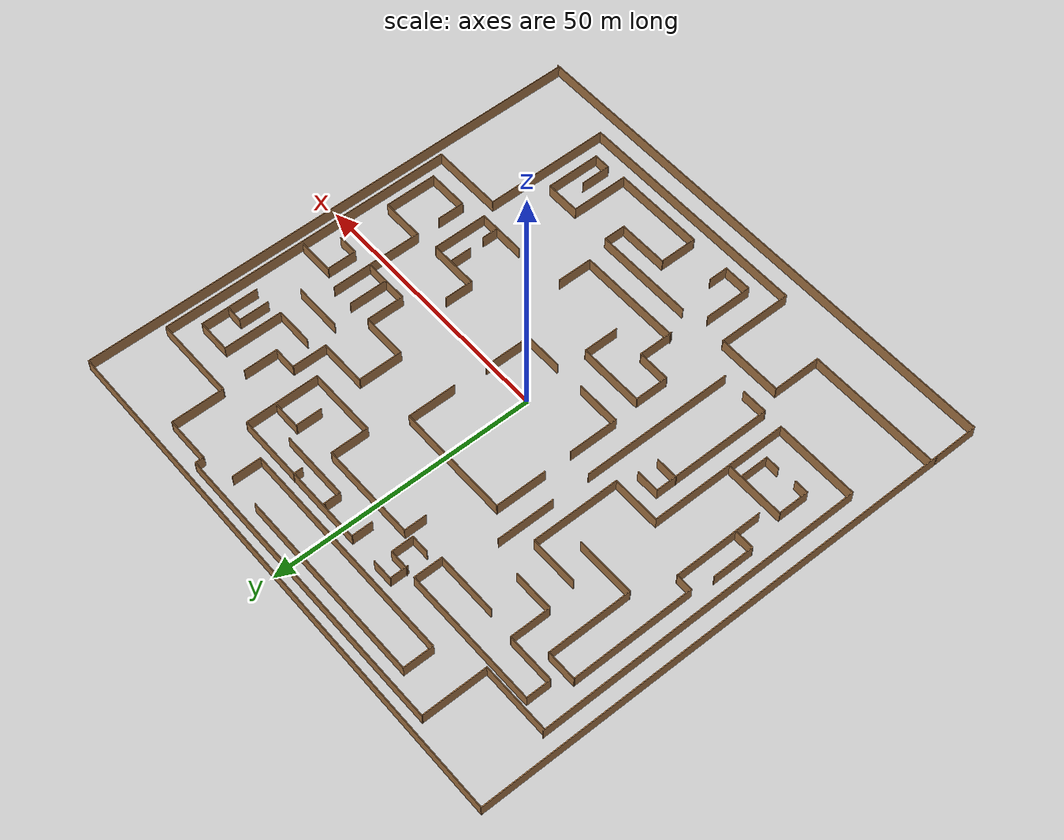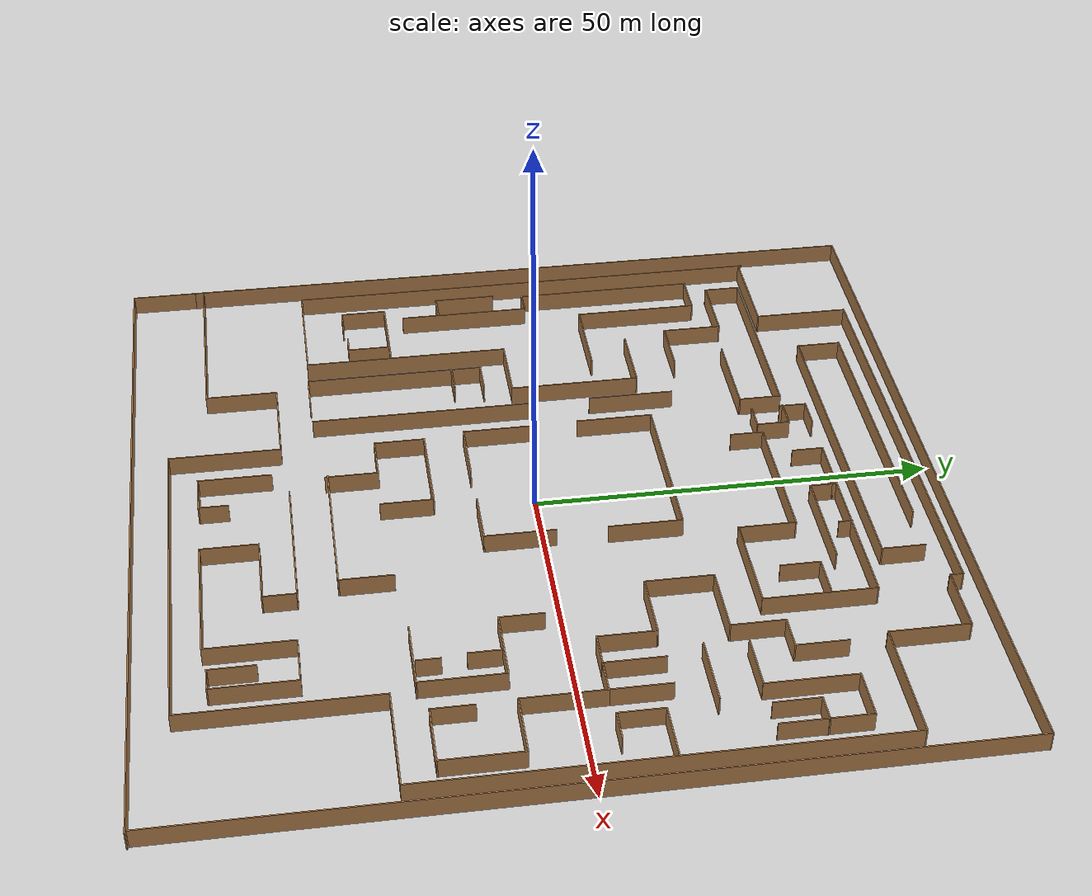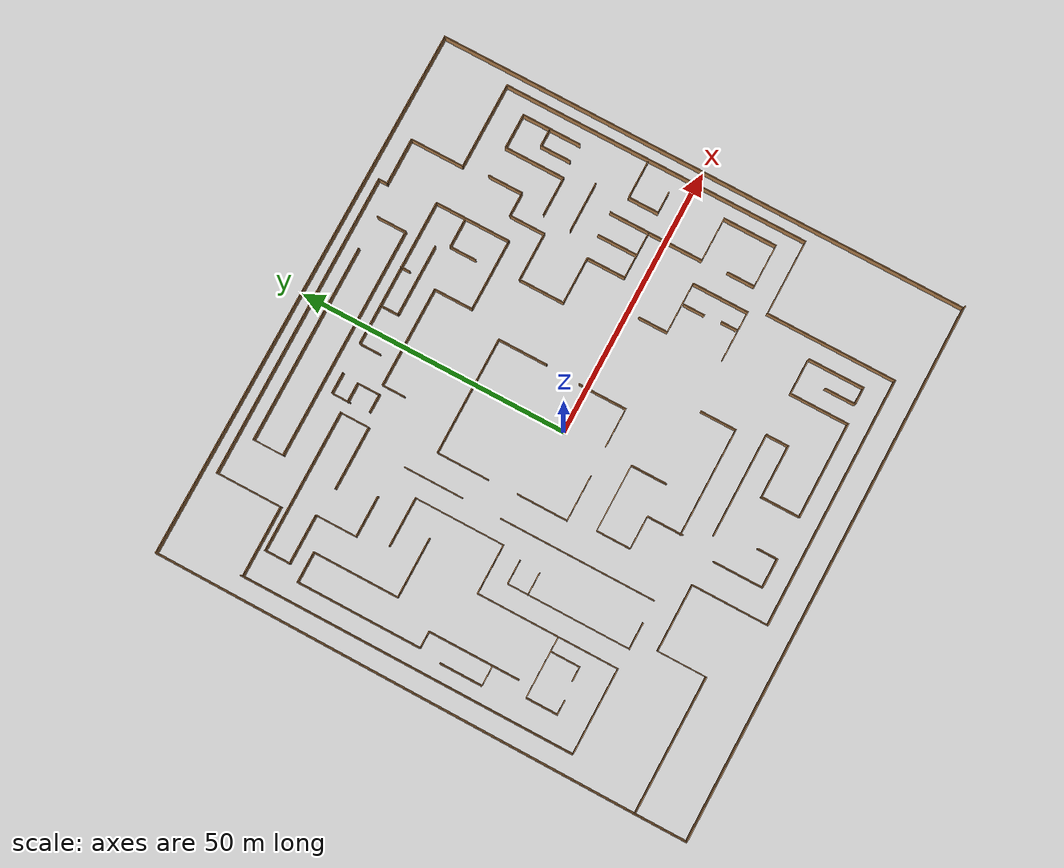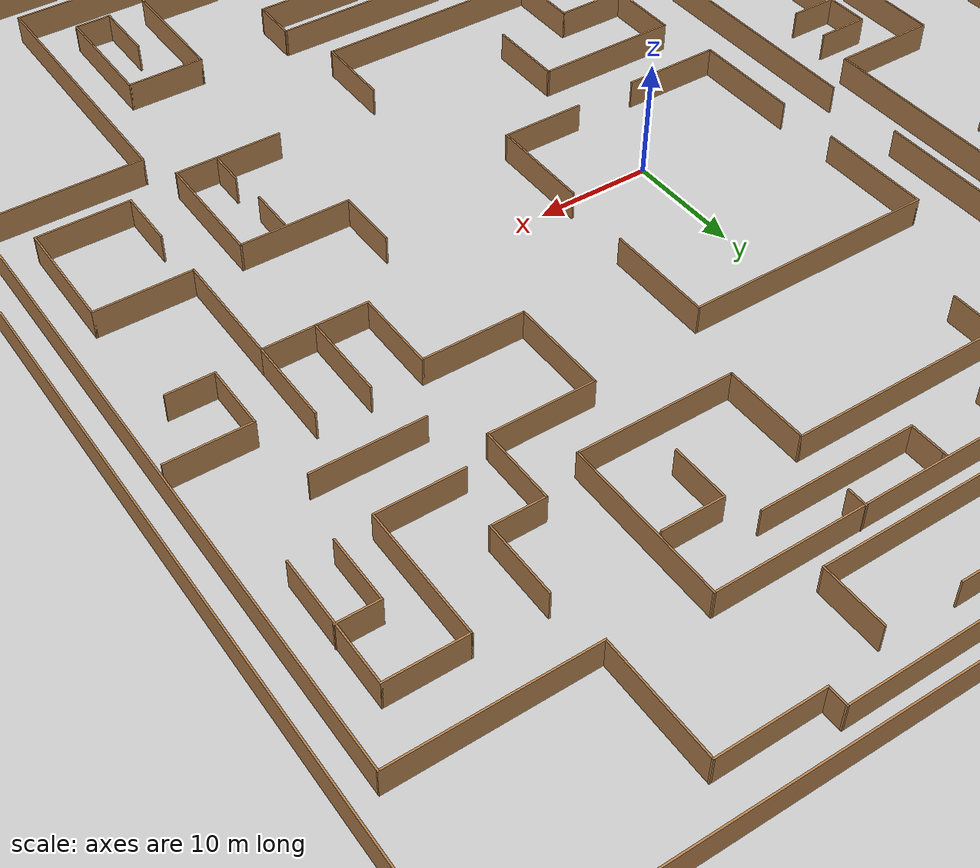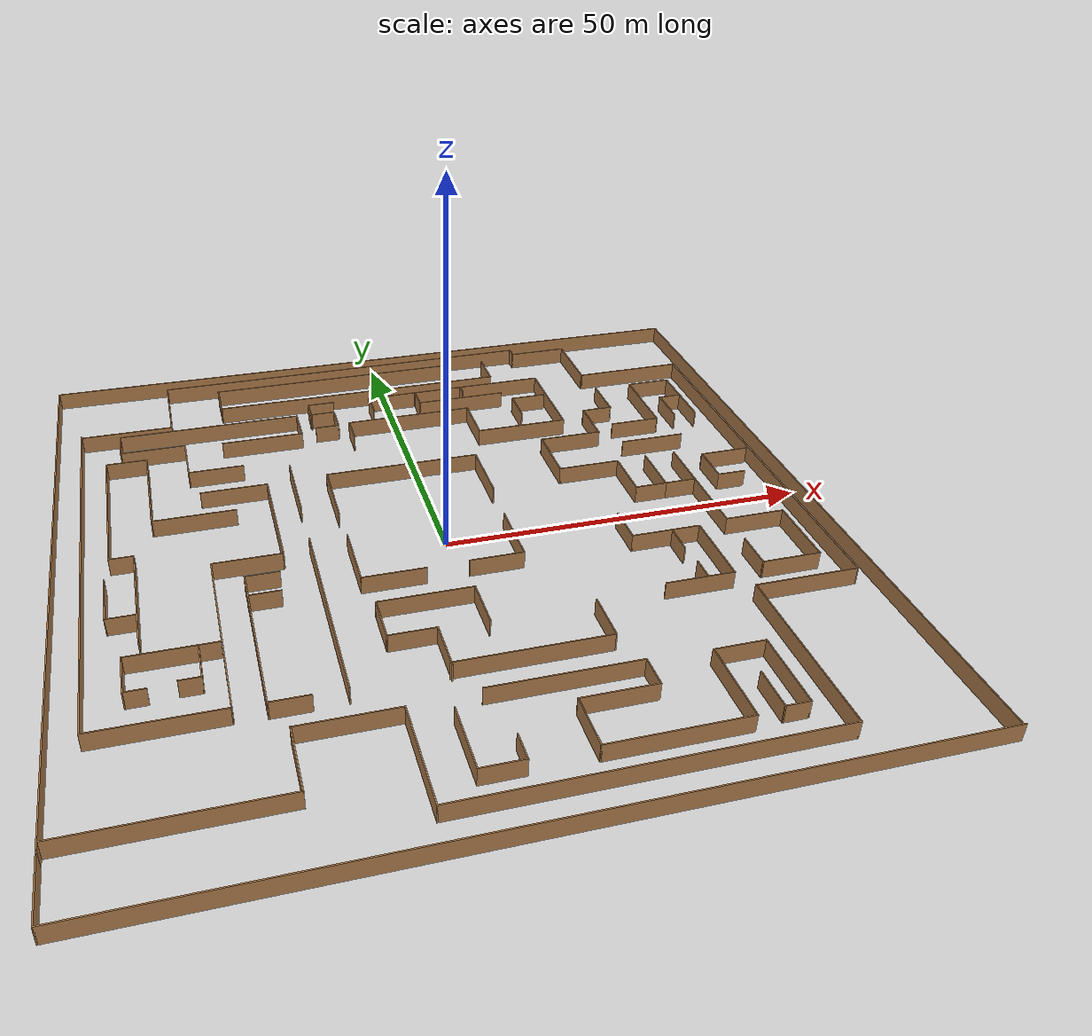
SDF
<?xml version='1.0'?>
<sdf version='1.7'>
  <model name='model4'>
    <pose>0.113714 0.358597 0 0 -0 0</pose>
    <link name='Wall_100'>
      <collision name='Wall_100_Collision'>
        <geometry>
          <box>
            <size>26.25 0.15 2.5</size>
          </box>
        </geometry>
        <pose>0 0 1.25 0 -0 0</pose>
      </collision>
      <visual name='Wall_100_Visual'>
        <pose>0 0 1.25 0 -0 0</pose>
        <geometry>
          <box>
            <size>26.25 0.15 2.5</size>
          </box>
        </geometry>
        <material>
          <script>
            <uri>file://media/materials/scripts/gazebo.material</uri>
            <name>Gazebo/Wood</name>
          </script>
          <ambient>1 1 1 1</ambient>
        </material>
        <meta>
          <layer>0</layer>
        </meta>
      </visual>
      <pose>-27.882 34.0515 0 0 -0 0</pose>
    </link>
    <link name='Wall_101'>
      <collision name='Wall_101_Collision'>
        <geometry>
          <box>
            <size>5.5 0.15 2.5</size>
          </box>
        </geometry>
        <pose>0 0 1.25 0 -0 0</pose>
      </collision>
      <visual name='Wall_101_Visual'>
        <pose>0 0 1.25 0 -0 0</pose>
        <geometry>
          <box>
            <size>5.5 0.15 2.5</size>
          </box>
        </geometry>
        <material>
          <script>
            <uri>file://media/materials/scripts/gazebo.material</uri>
            <name>Gazebo/Wood</name>
          </script>
          <ambient>1 1 1 1</ambient>
        </material>
        <meta>
          <layer>0</layer>
        </meta>
      </visual>
      <pose>-14.832 31.3765 0 0 -0 -1.5708</pose>
    </link>
    <link name='Wall_102'>
      <collision name='Wall_102_Collision'>
        <geometry>
          <box>
            <size>11.75 0.15 2.5</size>
          </box>
        </geometry>
        <pose>0 0 1.25 0 -0 0</pose>
      </collision>
      <visual name='Wall_102_Visual'>
        <pose>0 0 1.25 0 -0 0</pose>
        <geometry>
          <box>
            <size>11.75 0.15 2.5</size>
          </box>
        </geometry>
        <material>
          <script>
            <uri>file://media/materials/scripts/gazebo.material</uri>
            <name>Gazebo/Wood</name>
          </script>
          <ambient>1 1 1 1</ambient>
        </material>
        <meta>
          <layer>0</layer>
        </meta>
      </visual>
      <pose>-20.632 28.7015 0 0 -0 3.14159</pose>
    </link>
    <link name='Wall_104'>
      <collision name='Wall_104_Collision'>
        <geometry>
          <box>
            <size>5.5 0.15 2.5</size>
          </box>
        </geometry>
        <pose>0 0 1.25 0 -0 0</pose>
      </collision>
      <visual name='Wall_104_Visual'>
        <pose>0 0 1.25 0 -0 0</pose>
        <geometry>
          <box>
            <size>5.5 0.15 2.5</size>
          </box>
        </geometry>
        <material>
          <script>
            <uri>file://media/materials/scripts/gazebo.material</uri>
            <name>Gazebo/Wood</name>
          </script>
          <ambient>1 1 1 1</ambient>
        </material>
        <meta>
          <layer>0</layer>
        </meta>
      </visual>
      <pose>17.1753 41.7624 0 0 -0 -1.5708</pose>
    </link>
    <link name='Wall_105'>
      <collision name='Wall_105_Collision'>
        <geometry>
          <box>
            <size>43 0.15 2.5</size>
          </box>
        </geometry>
        <pose>0 0 1.25 0 -0 0</pose>
      </collision>
      <visual name='Wall_105_Visual'>
        <pose>0 0 1.25 0 -0 0</pose>
        <geometry>
          <box>
            <size>43 0.15 2.5</size>
          </box>
        </geometry>
        <material>
          <script>
            <uri>file://media/materials/scripts/gazebo.material</uri>
            <name>Gazebo/Wood</name>
          </script>
          <ambient>1 1 1 1</ambient>
        </material>
        <meta>
          <layer>0</layer>
        </meta>
      </visual>
      <pose>-4.24968 39.0874 0 0 -0 3.14159</pose>
    </link>
    <link name='Wall_106'>
      <collision name='Wall_106_Collision'>
        <geometry>
          <box>
            <size>5.75 0.15 2.5</size>
          </box>
        </geometry>
        <pose>0 0 1.25 0 -0 0</pose>
      </collision>
      <visual name='Wall_106_Visual'>
        <pose>0 0 1.25 0 -0 0</pose>
        <geometry>
          <box>
            <size>5.75 0.15 2.5</size>
          </box>
        </geometry>
        <material>
          <script>
            <uri>file://media/materials/scripts/gazebo.material</uri>
            <name>Gazebo/Wood</name>
          </script>
          <ambient>1 1 1 1</ambient>
        </material>
        <meta>
          <layer>0</layer>
        </meta>
      </visual>
      <pose>-25.6747 41.8874 0 0 -0 1.5708</pose>
    </link>
    <link name='Wall_107'>
      <collision name='Wall_107_Collision'>
        <geometry>
          <box>
            <size>36.75 0.15 2.5</size>
          </box>
        </geometry>
        <pose>0 0 1.25 0 -0 0</pose>
      </collision>
      <visual name='Wall_107_Visual'>
        <pose>0 0 1.25 0 -0 0</pose>
        <geometry>
          <box>
            <size>36.75 0.15 2.5</size>
          </box>
        </geometry>
        <material>
          <script>
            <uri>file://media/materials/scripts/gazebo.material</uri>
            <name>Gazebo/Wood</name>
          </script>
          <ambient>1 1 1 1</ambient>
        </material>
        <meta>
          <layer>0</layer>
        </meta>
      </visual>
      <pose>-7.37468 44.6874 0 0 -0 0</pose>
    </link>
    <link name='Wall_109'>
      <collision name='Wall_109_Collision'>
        <geometry>
          <box>
            <size>4.25 0.15 2.5</size>
          </box>
        </geometry>
        <pose>0 0 1.25 0 -0 0</pose>
      </collision>
      <visual name='Wall_109_Visual'>
        <pose>0 0 1.25 0 -0 0</pose>
        <geometry>
          <box>
            <size>4.25 0.15 2.5</size>
          </box>
        </geometry>
        <material>
          <script>
            <uri>file://media/materials/scripts/gazebo.material</uri>
            <name>Gazebo/Wood</name>
          </script>
          <ambient>1 1 1 1</ambient>
        </material>
        <meta>
          <layer>0</layer>
        </meta>
      </visual>
      <pose>-7.48087 28.0423 0 0 -0 1.5708</pose>
    </link>
    <link name='Wall_110'>
      <collision name='Wall_110_Collision'>
        <geometry>
          <box>
            <size>18.5 0.15 2.5</size>
          </box>
        </geometry>
        <pose>0 0 1.25 0 -0 0</pose>
      </collision>
      <visual name='Wall_110_Visual'>
        <pose>0 0 1.25 0 -0 0</pose>
        <geometry>
          <box>
            <size>18.5 0.15 2.5</size>
          </box>
        </geometry>
        <material>
          <script>
            <uri>file://media/materials/scripts/gazebo.material</uri>
            <name>Gazebo/Wood</name>
          </script>
          <ambient>1 1 1 1</ambient>
        </material>
        <meta>
          <layer>0</layer>
        </meta>
      </visual>
      <pose>1.69413 30.0923 0 0 -0 0</pose>
    </link>
    <link name='Wall_111'>
      <collision name='Wall_111_Collision'>
        <geometry>
          <box>
            <size>7.25 0.15 2.5</size>
          </box>
        </geometry>
        <pose>0 0 1.25 0 -0 0</pose>
      </collision>
      <visual name='Wall_111_Visual'>
        <pose>0 0 1.25 0 -0 0</pose>
        <geometry>
          <box>
            <size>7.25 0.15 2.5</size>
          </box>
        </geometry>
        <material>
          <script>
            <uri>file://media/materials/scripts/gazebo.material</uri>
            <name>Gazebo/Wood</name>
          </script>
          <ambient>1 1 1 1</ambient>
        </material>
        <meta>
          <layer>0</layer>
        </meta>
      </visual>
      <pose>10.8691 26.5423 0 0 -0 -1.5708</pose>
    </link>
    <link name='Wall_112'>
      <collision name='Wall_112_Collision'>
        <geometry>
          <box>
            <size>13.25 0.15 2.5</size>
          </box>
        </geometry>
        <pose>0 0 1.25 0 -0 0</pose>
      </collision>
      <visual name='Wall_112_Visual'>
        <pose>0 0 1.25 0 -0 0</pose>
        <geometry>
          <box>
            <size>13.25 0.15 2.5</size>
          </box>
        </geometry>
        <material>
          <script>
            <uri>file://media/materials/scripts/gazebo.material</uri>
            <name>Gazebo/Wood</name>
          </script>
          <ambient>1 1 1 1</ambient>
        </material>
        <meta>
          <layer>0</layer>
        </meta>
      </visual>
      <pose>17.4191 22.9923 0 0 -0 0</pose>
    </link>
    <link name='Wall_113'>
      <collision name='Wall_113_Collision'>
        <geometry>
          <box>
            <size>14 0.15 2.5</size>
          </box>
        </geometry>
        <pose>0 0 1.25 0 -0 0</pose>
      </collision>
      <visual name='Wall_113_Visual'>
        <pose>0 0 1.25 0 -0 0</pose>
        <geometry>
          <box>
            <size>14 0.15 2.5</size>
          </box>
        </geometry>
        <material>
          <script>
            <uri>file://media/materials/scripts/gazebo.material</uri>
            <name>Gazebo/Wood</name>
          </script>
          <ambient>1 1 1 1</ambient>
        </material>
        <meta>
          <layer>0</layer>
        </meta>
      </visual>
      <pose>23.9691 29.9173 0 0 -0 1.5708</pose>
    </link>
    <link name='Wall_114'>
      <collision name='Wall_114_Collision'>
        <geometry>
          <box>
            <size>27.25 0.15 2.5</size>
          </box>
        </geometry>
        <pose>0 0 1.25 0 -0 0</pose>
      </collision>
      <visual name='Wall_114_Visual'>
        <pose>0 0 1.25 0 -0 0</pose>
        <geometry>
          <box>
            <size>27.25 0.15 2.5</size>
          </box>
        </geometry>
        <material>
          <script>
            <uri>file://media/materials/scripts/gazebo.material</uri>
            <name>Gazebo/Wood</name>
          </script>
          <ambient>1 1 1 1</ambient>
        </material>
        <meta>
          <layer>0</layer>
        </meta>
      </visual>
      <pose>10.4191 36.8423 0 0 -0 3.14159</pose>
    </link>
    <link name='Wall_115'>
      <collision name='Wall_115_Collision'>
        <geometry>
          <box>
            <size>4 0.15 2.5</size>
          </box>
        </geometry>
        <pose>0 0 1.25 0 -0 0</pose>
      </collision>
      <visual name='Wall_115_Visual'>
        <pose>0 0 1.25 0 -0 0</pose>
        <geometry>
          <box>
            <size>4 0.15 2.5</size>
          </box>
        </geometry>
        <material>
          <script>
            <uri>file://media/materials/scripts/gazebo.material</uri>
            <name>Gazebo/Wood</name>
          </script>
          <ambient>1 1 1 1</ambient>
        </material>
        <meta>
          <layer>0</layer>
        </meta>
      </visual>
      <pose>-3.13087 34.9173 0 0 -0 -1.5708</pose>
    </link>
    <link name='Wall_117'>
      <collision name='Wall_117_Collision'>
        <geometry>
          <box>
            <size>3 0.15 2.5</size>
          </box>
        </geometry>
        <pose>0 0 1.25 0 -0 0</pose>
      </collision>
      <visual name='Wall_117_Visual'>
        <pose>0 0 1.25 0 -0 0</pose>
        <geometry>
          <box>
            <size>3 0.15 2.5</size>
          </box>
        </geometry>
        <material>
          <script>
            <uri>file://media/materials/scripts/gazebo.material</uri>
            <name>Gazebo/Wood</name>
          </script>
          <ambient>1 1 1 1</ambient>
        </material>
        <meta>
          <layer>0</layer>
        </meta>
      </visual>
      <pose>4.18847 34.9191 0 0 -0 -1.5708</pose>
    </link>
    <link name='Wall_118'>
      <collision name='Wall_118_Collision'>
        <geometry>
          <box>
            <size>13.25 0.15 2.5</size>
          </box>
        </geometry>
        <pose>0 0 1.25 0 -0 0</pose>
      </collision>
      <visual name='Wall_118_Visual'>
        <pose>0 0 1.25 0 -0 0</pose>
        <geometry>
          <box>
            <size>13.25 0.15 2.5</size>
          </box>
        </geometry>
        <material>
          <script>
            <uri>file://media/materials/scripts/gazebo.material</uri>
            <name>Gazebo/Wood</name>
          </script>
          <ambient>1 1 1 1</ambient>
        </material>
        <meta>
          <layer>0</layer>
        </meta>
      </visual>
      <pose>10.7385 33.4941 0 0 -0 0</pose>
    </link>
    <link name='Wall_121'>
      <collision name='Wall_121_Collision'>
        <geometry>
          <box>
            <size>1.75 0.15 2.5</size>
          </box>
        </geometry>
        <pose>0 0 1.25 0 -0 0</pose>
      </collision>
      <visual name='Wall_121_Visual'>
        <pose>0 0 1.25 0 -0 0</pose>
        <geometry>
          <box>
            <size>1.75 0.15 2.5</size>
          </box>
        </geometry>
        <material>
          <script>
            <uri>file://media/materials/scripts/gazebo.material</uri>
            <name>Gazebo/Wood</name>
          </script>
          <ambient>1 1 1 1</ambient>
        </material>
        <meta>
          <layer>0</layer>
        </meta>
      </visual>
      <pose>11.5289 36.1088 0 0 -0 -1.5708</pose>
    </link>
    <link name='Wall_123'>
      <collision name='Wall_123_Collision'>
        <geometry>
          <box>
            <size>0.5 0.15 2.5</size>
          </box>
        </geometry>
        <pose>0 0 1.25 0 -0 0</pose>
      </collision>
      <visual name='Wall_123_Visual'>
        <pose>0 0 1.25 0 -0 0</pose>
        <geometry>
          <box>
            <size>0.5 0.15 2.5</size>
          </box>
        </geometry>
        <material>
          <script>
            <uri>file://media/materials/scripts/gazebo.material</uri>
            <name>Gazebo/Wood</name>
          </script>
          <ambient>1 1 1 1</ambient>
        </material>
        <meta>
          <layer>0</layer>
        </meta>
      </visual>
      <pose>4.18847 36.5191 0 0 -0 1.5708</pose>
    </link>
    <link name='Wall_125'>
      <collision name='Wall_125_Collision'>
        <geometry>
          <box>
            <size>5.25 0.15 2.5</size>
          </box>
        </geometry>
        <pose>0 0 1.25 0 -0 0</pose>
      </collision>
      <visual name='Wall_125_Visual'>
        <pose>0 0 1.25 0 -0 0</pose>
        <geometry>
          <box>
            <size>5.25 0.15 2.5</size>
          </box>
        </geometry>
        <material>
          <script>
            <uri>file://media/materials/scripts/gazebo.material</uri>
            <name>Gazebo/Wood</name>
          </script>
          <ambient>1 1 1 1</ambient>
        </material>
        <meta>
          <layer>0</layer>
        </meta>
      </visual>
      <pose>21.0246 31.2623 0 0 -0 3.14159</pose>
    </link>
    <link name='Wall_126'>
      <collision name='Wall_126_Collision'>
        <geometry>
          <box>
            <size>5 0.15 2.5</size>
          </box>
        </geometry>
        <pose>0 0 1.25 0 -0 0</pose>
      </collision>
      <visual name='Wall_126_Visual'>
        <pose>0 0 1.25 0 -0 0</pose>
        <geometry>
          <box>
            <size>5 0.15 2.5</size>
          </box>
        </geometry>
        <material>
          <script>
            <uri>file://media/materials/scripts/gazebo.material</uri>
            <name>Gazebo/Wood</name>
          </script>
          <ambient>1 1 1 1</ambient>
        </material>
        <meta>
          <layer>0</layer>
        </meta>
      </visual>
      <pose>18.4746 28.8373 0 0 -0 -1.5708</pose>
    </link>
    <link name='Wall_129'>
      <collision name='Wall_129_Collision'>
        <geometry>
          <box>
            <size>4 0.15 2.5</size>
          </box>
        </geometry>
        <pose>0 0 1.25 0 -0 0</pose>
      </collision>
      <visual name='Wall_129_Visual'>
        <pose>0 0 1.25 0 -0 0</pose>
        <geometry>
          <box>
            <size>4 0.15 2.5</size>
          </box>
        </geometry>
        <material>
          <script>
            <uri>file://media/materials/scripts/gazebo.material</uri>
            <name>Gazebo/Wood</name>
          </script>
          <ambient>1 1 1 1</ambient>
        </material>
        <meta>
          <layer>0</layer>
        </meta>
      </visual>
      <pose>-10.7234 36.9088 0 0 -0 3.14159</pose>
    </link>
    <link name='Wall_130'>
      <collision name='Wall_130_Collision'>
        <geometry>
          <box>
            <size>3.5 0.15 2.5</size>
          </box>
        </geometry>
        <pose>0 0 1.25 0 -0 0</pose>
      </collision>
      <visual name='Wall_130_Visual'>
        <pose>0 0 1.25 0 -0 0</pose>
        <geometry>
          <box>
            <size>3.5 0.15 2.5</size>
          </box>
        </geometry>
        <material>
          <script>
            <uri>file://media/materials/scripts/gazebo.material</uri>
            <name>Gazebo/Wood</name>
          </script>
          <ambient>1 1 1 1</ambient>
        </material>
        <meta>
          <layer>0</layer>
        </meta>
      </visual>
      <pose>-12.6484 35.2338 0 0 -0 -1.5708</pose>
    </link>
    <link name='Wall_133'>
      <collision name='Wall_133_Collision'>
        <geometry>
          <box>
            <size>3.75 0.15 2.5</size>
          </box>
        </geometry>
        <pose>0 0 1.25 0 -0 0</pose>
      </collision>
      <visual name='Wall_133_Visual'>
        <pose>0 0 1.25 0 -0 0</pose>
        <geometry>
          <box>
            <size>3.75 0.15 2.5</size>
          </box>
        </geometry>
        <material>
          <script>
            <uri>file://media/materials/scripts/gazebo.material</uri>
            <name>Gazebo/Wood</name>
          </script>
          <ambient>1 1 1 1</ambient>
        </material>
        <meta>
          <layer>0</layer>
        </meta>
      </visual>
      <pose>-10.9509 33.8973 0 0 -0 0</pose>
    </link>
    <link name='Wall_134'>
      <collision name='Wall_134_Collision'>
        <geometry>
          <box>
            <size>4.25 0.15 2.5</size>
          </box>
        </geometry>
        <pose>0 0 1.25 0 -0 0</pose>
      </collision>
      <visual name='Wall_134_Visual'>
        <pose>0 0 1.25 0 -0 0</pose>
        <geometry>
          <box>
            <size>4.25 0.15 2.5</size>
          </box>
        </geometry>
        <material>
          <script>
            <uri>file://media/materials/scripts/gazebo.material</uri>
            <name>Gazebo/Wood</name>
          </script>
          <ambient>1 1 1 1</ambient>
        </material>
        <meta>
          <layer>0</layer>
        </meta>
      </visual>
      <pose>-9.1509 31.8473 0 0 -0 -1.5708</pose>
    </link>
    <link name='Wall_135'>
      <collision name='Wall_135_Collision'>
        <geometry>
          <box>
            <size>3.5 0.15 2.5</size>
          </box>
        </geometry>
        <pose>0 0 1.25 0 -0 0</pose>
      </collision>
      <visual name='Wall_135_Visual'>
        <pose>0 0 1.25 0 -0 0</pose>
        <geometry>
          <box>
            <size>3.5 0.15 2.5</size>
          </box>
        </geometry>
        <material>
          <script>
            <uri>file://media/materials/scripts/gazebo.material</uri>
            <name>Gazebo/Wood</name>
          </script>
          <ambient>1 1 1 1</ambient>
        </material>
        <meta>
          <layer>0</layer>
        </meta>
      </visual>
      <pose>-10.8259 29.7973 0 0 -0 3.14159</pose>
    </link>
    <link name='Wall_139'>
      <collision name='Wall_139_Collision'>
        <geometry>
          <box>
            <size>9.25 0.15 2.5</size>
          </box>
        </geometry>
        <pose>0 0 1.25 0 -0 0</pose>
      </collision>
      <visual name='Wall_139_Visual'>
        <pose>0 0 1.25 0 -0 0</pose>
        <geometry>
          <box>
            <size>9.25 0.15 2.5</size>
          </box>
        </geometry>
        <material>
          <script>
            <uri>file://media/materials/scripts/gazebo.material</uri>
            <name>Gazebo/Wood</name>
          </script>
          <ambient>1 1 1 1</ambient>
        </material>
        <meta>
          <layer>0</layer>
        </meta>
      </visual>
      <pose>-7.48087 -37.0926 0 0 -0 -1.5708</pose>
    </link>
    <link name='Wall_140'>
      <collision name='Wall_140_Collision'>
        <geometry>
          <box>
            <size>5.5 0.15 2.5</size>
          </box>
        </geometry>
        <pose>0 0 1.25 0 -0 0</pose>
      </collision>
      <visual name='Wall_140_Visual'>
        <pose>0 0 1.25 0 -0 0</pose>
        <geometry>
          <box>
            <size>5.5 0.15 2.5</size>
          </box>
        </geometry>
        <material>
          <script>
            <uri>file://media/materials/scripts/gazebo.material</uri>
            <name>Gazebo/Wood</name>
          </script>
          <ambient>1 1 1 1</ambient>
        </material>
        <meta>
          <layer>0</layer>
        </meta>
      </visual>
      <pose>-4.80587 -41.6427 0 0 -0 0</pose>
    </link>
    <link name='Wall_141'>
      <collision name='Wall_141_Collision'>
        <geometry>
          <box>
            <size>3.75 0.15 2.5</size>
          </box>
        </geometry>
        <pose>0 0 1.25 0 -0 0</pose>
      </collision>
      <visual name='Wall_141_Visual'>
        <pose>0 0 1.25 0 -0 0</pose>
        <geometry>
          <box>
            <size>3.75 0.15 2.5</size>
          </box>
        </geometry>
        <material>
          <script>
            <uri>file://media/materials/scripts/gazebo.material</uri>
            <name>Gazebo/Wood</name>
          </script>
          <ambient>1 1 1 1</ambient>
        </material>
        <meta>
          <layer>0</layer>
        </meta>
      </visual>
      <pose>-2.13087 -39.8426 0 0 -0 1.5708</pose>
    </link>
    <link name='Wall_143'>
      <collision name='Wall_143_Collision'>
        <geometry>
          <box>
            <size>19.25 0.15 2.5</size>
          </box>
        </geometry>
        <pose>0 0 1.25 0 -0 0</pose>
      </collision>
      <visual name='Wall_143_Visual'>
        <pose>0 0 1.25 0 -0 0</pose>
        <geometry>
          <box>
            <size>19.25 0.15 2.5</size>
          </box>
        </geometry>
        <material>
          <script>
            <uri>file://media/materials/scripts/gazebo.material</uri>
            <name>Gazebo/Wood</name>
          </script>
          <ambient>1 1 1 1</ambient>
        </material>
        <meta>
          <layer>0</layer>
        </meta>
      </visual>
      <pose>5.83343 -30.4723 0 0 -0 0</pose>
    </link>
    <link name='Wall_144'>
      <collision name='Wall_144_Collision'>
        <geometry>
          <box>
            <size>4.25 0.15 2.5</size>
          </box>
        </geometry>
        <pose>0 0 1.25 0 -0 0</pose>
      </collision>
      <visual name='Wall_144_Visual'>
        <pose>0 0 1.25 0 -0 0</pose>
        <geometry>
          <box>
            <size>4.25 0.15 2.5</size>
          </box>
        </geometry>
        <material>
          <script>
            <uri>file://media/materials/scripts/gazebo.material</uri>
            <name>Gazebo/Wood</name>
          </script>
          <ambient>1 1 1 1</ambient>
        </material>
        <meta>
          <layer>0</layer>
        </meta>
      </visual>
      <pose>15.3834 -32.5223 0 0 -0 -1.5708</pose>
    </link>
    <link name='Wall_145'>
      <collision name='Wall_145_Collision'>
        <geometry>
          <box>
            <size>9.75 0.15 2.5</size>
          </box>
        </geometry>
        <pose>0 0 1.25 0 -0 0</pose>
      </collision>
      <visual name='Wall_145_Visual'>
        <pose>0 0 1.25 0 -0 0</pose>
        <geometry>
          <box>
            <size>9.75 0.15 2.5</size>
          </box>
        </geometry>
        <material>
          <script>
            <uri>file://media/materials/scripts/gazebo.material</uri>
            <name>Gazebo/Wood</name>
          </script>
          <ambient>1 1 1 1</ambient>
        </material>
        <meta>
          <layer>0</layer>
        </meta>
      </visual>
      <pose>10.5834 -34.5723 0 0 -0 3.14159</pose>
    </link>
    <link name='Wall_146'>
      <collision name='Wall_146_Collision'>
        <geometry>
          <box>
            <size>7.25 0.15 2.5</size>
          </box>
        </geometry>
        <pose>0 0 1.25 0 -0 0</pose>
      </collision>
      <visual name='Wall_146_Visual'>
        <pose>0 0 1.25 0 -0 0</pose>
        <geometry>
          <box>
            <size>7.25 0.15 2.5</size>
          </box>
        </geometry>
        <material>
          <script>
            <uri>file://media/materials/scripts/gazebo.material</uri>
            <name>Gazebo/Wood</name>
          </script>
          <ambient>1 1 1 1</ambient>
        </material>
        <meta>
          <layer>0</layer>
        </meta>
      </visual>
      <pose>5.78343 -38.1223 0 0 -0 -1.5708</pose>
    </link>
    <link name='Wall_147'>
      <collision name='Wall_147_Collision'>
        <geometry>
          <box>
            <size>17.75 0.15 2.5</size>
          </box>
        </geometry>
        <pose>0 0 1.25 0 -0 0</pose>
      </collision>
      <visual name='Wall_147_Visual'>
        <pose>0 0 1.25 0 -0 0</pose>
        <geometry>
          <box>
            <size>17.75 0.15 2.5</size>
          </box>
        </geometry>
        <material>
          <script>
            <uri>file://media/materials/scripts/gazebo.material</uri>
            <name>Gazebo/Wood</name>
          </script>
          <ambient>1 1 1 1</ambient>
        </material>
        <meta>
          <layer>0</layer>
        </meta>
      </visual>
      <pose>14.5834 -41.6723 0 0 -0 0</pose>
    </link>
    <link name='Wall_148'>
      <collision name='Wall_148_Collision'>
        <geometry>
          <box>
            <size>11 0.15 2.5</size>
          </box>
        </geometry>
        <pose>0 0 1.25 0 -0 0</pose>
      </collision>
      <visual name='Wall_148_Visual'>
        <pose>0 0 1.25 0 -0 0</pose>
        <geometry>
          <box>
            <size>11 0.15 2.5</size>
          </box>
        </geometry>
        <material>
          <script>
            <uri>file://media/materials/scripts/gazebo.material</uri>
            <name>Gazebo/Wood</name>
          </script>
          <ambient>1 1 1 1</ambient>
        </material>
        <meta>
          <layer>0</layer>
        </meta>
      </visual>
      <pose>23.3834 -36.2473 0 0 -0 1.5708</pose>
    </link>
    <link name='Wall_149'>
      <collision name='Wall_149_Collision'>
        <geometry>
          <box>
            <size>6.75 0.15 2.5</size>
          </box>
        </geometry>
        <pose>0 0 1.25 0 -0 0</pose>
      </collision>
      <visual name='Wall_149_Visual'>
        <pose>0 0 1.25 0 -0 0</pose>
        <geometry>
          <box>
            <size>6.75 0.15 2.5</size>
          </box>
        </geometry>
        <material>
          <script>
            <uri>file://media/materials/scripts/gazebo.material</uri>
            <name>Gazebo/Wood</name>
          </script>
          <ambient>1 1 1 1</ambient>
        </material>
        <meta>
          <layer>0</layer>
        </meta>
      </visual>
      <pose>26.6834 -30.8223 0 0 -0 0</pose>
    </link>
    <link name='Wall_150'>
      <collision name='Wall_150_Collision'>
        <geometry>
          <box>
            <size>10.5 0.15 2.5</size>
          </box>
        </geometry>
        <pose>0 0 1.25 0 -0 0</pose>
      </collision>
      <visual name='Wall_150_Visual'>
        <pose>0 0 1.25 0 -0 0</pose>
        <geometry>
          <box>
            <size>10.5 0.15 2.5</size>
          </box>
        </geometry>
        <material>
          <script>
            <uri>file://media/materials/scripts/gazebo.material</uri>
            <name>Gazebo/Wood</name>
          </script>
          <ambient>1 1 1 1</ambient>
        </material>
        <meta>
          <layer>0</layer>
        </meta>
      </visual>
      <pose>29.9834 -35.9973 0 0 -0 -1.5708</pose>
    </link>
    <link name='Wall_151'>
      <collision name='Wall_151_Collision'>
        <geometry>
          <box>
            <size>3.25 0.15 2.5</size>
          </box>
        </geometry>
        <pose>0 0 1.25 0 -0 0</pose>
      </collision>
      <visual name='Wall_151_Visual'>
        <pose>0 0 1.25 0 -0 0</pose>
        <geometry>
          <box>
            <size>3.25 0.15 2.5</size>
          </box>
        </geometry>
        <material>
          <script>
            <uri>file://media/materials/scripts/gazebo.material</uri>
            <name>Gazebo/Wood</name>
          </script>
          <ambient>1 1 1 1</ambient>
        </material>
        <meta>
          <layer>0</layer>
        </meta>
      </visual>
      <pose>28.4334 -41.1723 0 0 -0 3.14159</pose>
    </link>
    <link name='Wall_152'>
      <collision name='Wall_152_Collision'>
        <geometry>
          <box>
            <size>5.75 0.15 2.5</size>
          </box>
        </geometry>
        <pose>0 0 1.25 0 -0 0</pose>
      </collision>
      <visual name='Wall_152_Visual'>
        <pose>0 0 1.25 0 -0 0</pose>
        <geometry>
          <box>
            <size>5.75 0.15 2.5</size>
          </box>
        </geometry>
        <material>
          <script>
            <uri>file://media/materials/scripts/gazebo.material</uri>
            <name>Gazebo/Wood</name>
          </script>
          <ambient>1 1 1 1</ambient>
        </material>
        <meta>
          <layer>0</layer>
        </meta>
      </visual>
      <pose>26.8834 -38.3723 0 0 -0 1.5708</pose>
    </link>
    <link name='Wall_154'>
      <collision name='Wall_154_Collision'>
        <geometry>
          <box>
            <size>6.75 0.15 2.5</size>
          </box>
        </geometry>
        <pose>0 0 1.25 0 -0 0</pose>
      </collision>
      <visual name='Wall_154_Visual'>
        <pose>0 0 1.25 0 -0 0</pose>
        <geometry>
          <box>
            <size>6.75 0.15 2.5</size>
          </box>
        </geometry>
        <material>
          <script>
            <uri>file://media/materials/scripts/gazebo.material</uri>
            <name>Gazebo/Wood</name>
          </script>
          <ambient>1 1 1 1</ambient>
        </material>
        <meta>
          <layer>0</layer>
        </meta>
      </visual>
      <pose>0.235952 -16.2558 0 0 -0 1.5708</pose>
    </link>
    <link name='Wall_155'>
      <collision name='Wall_155_Collision'>
        <geometry>
          <box>
            <size>12.5 0.15 2.5</size>
          </box>
        </geometry>
        <pose>0 0 1.25 0 -0 0</pose>
      </collision>
      <visual name='Wall_155_Visual'>
        <pose>0 0 1.25 0 -0 0</pose>
        <geometry>
          <box>
            <size>12.5 0.15 2.5</size>
          </box>
        </geometry>
        <material>
          <script>
            <uri>file://media/materials/scripts/gazebo.material</uri>
            <name>Gazebo/Wood</name>
          </script>
          <ambient>1 1 1 1</ambient>
        </material>
        <meta>
          <layer>0</layer>
        </meta>
      </visual>
      <pose>-5.93905 -12.9558 0 0 -0 3.14159</pose>
    </link>
    <link name='Wall_156'>
      <collision name='Wall_156_Collision'>
        <geometry>
          <box>
            <size>6.5 0.15 2.5</size>
          </box>
        </geometry>
        <pose>0 0 1.25 0 -0 0</pose>
      </collision>
      <visual name='Wall_156_Visual'>
        <pose>0 0 1.25 0 -0 0</pose>
        <geometry>
          <box>
            <size>6.5 0.15 2.5</size>
          </box>
        </geometry>
        <material>
          <script>
            <uri>file://media/materials/scripts/gazebo.material</uri>
            <name>Gazebo/Wood</name>
          </script>
          <ambient>1 1 1 1</ambient>
        </material>
        <meta>
          <layer>0</layer>
        </meta>
      </visual>
      <pose>-12.114 -16.1308 0 0 -0 -1.5708</pose>
    </link>
    <link name='Wall_157'>
      <collision name='Wall_157_Collision'>
        <geometry>
          <box>
            <size>6.25 0.15 2.5</size>
          </box>
        </geometry>
        <pose>0 0 1.25 0 -0 0</pose>
      </collision>
      <visual name='Wall_157_Visual'>
        <pose>0 0 1.25 0 -0 0</pose>
        <geometry>
          <box>
            <size>6.25 0.15 2.5</size>
          </box>
        </geometry>
        <material>
          <script>
            <uri>file://media/materials/scripts/gazebo.material</uri>
            <name>Gazebo/Wood</name>
          </script>
          <ambient>1 1 1 1</ambient>
        </material>
        <meta>
          <layer>0</layer>
        </meta>
      </visual>
      <pose>-9.06405 -19.3058 0 0 -0 0</pose>
    </link>
    <link name='Wall_158'>
      <collision name='Wall_158_Collision'>
        <geometry>
          <box>
            <size>6.75 0.15 2.5</size>
          </box>
        </geometry>
        <pose>0 0 1.25 0 -0 0</pose>
      </collision>
      <visual name='Wall_158_Visual'>
        <pose>0 0 1.25 0 -0 0</pose>
        <geometry>
          <box>
            <size>6.75 0.15 2.5</size>
          </box>
        </geometry>
        <material>
          <script>
            <uri>file://media/materials/scripts/gazebo.material</uri>
            <name>Gazebo/Wood</name>
          </script>
          <ambient>1 1 1 1</ambient>
        </material>
        <meta>
          <layer>0</layer>
        </meta>
      </visual>
      <pose>-6.01405 -22.6058 0 0 -0 -1.5708</pose>
    </link>
    <link name='Wall_160'>
      <collision name='Wall_160_Collision'>
        <geometry>
          <box>
            <size>20 0.15 2.5</size>
          </box>
        </geometry>
        <pose>0 0 1.25 0 -0 0</pose>
      </collision>
      <visual name='Wall_160_Visual'>
        <pose>0 0 1.25 0 -0 0</pose>
        <geometry>
          <box>
            <size>20 0.15 2.5</size>
          </box>
        </geometry>
        <material>
          <script>
            <uri>file://media/materials/scripts/gazebo.material</uri>
            <name>Gazebo/Wood</name>
          </script>
          <ambient>1 1 1 1</ambient>
        </material>
        <meta>
          <layer>0</layer>
        </meta>
      </visual>
      <pose>3.76164 -25.5787 0 0 -0 0</pose>
    </link>
    <link name='Wall_161'>
      <collision name='Wall_161_Collision'>
        <geometry>
          <box>
            <size>6.75 0.15 2.5</size>
          </box>
        </geometry>
        <pose>0 0 1.25 0 -0 0</pose>
      </collision>
      <visual name='Wall_161_Visual'>
        <pose>0 0 1.25 0 -0 0</pose>
        <geometry>
          <box>
            <size>6.75 0.15 2.5</size>
          </box>
        </geometry>
        <material>
          <script>
            <uri>file://media/materials/scripts/gazebo.material</uri>
            <name>Gazebo/Wood</name>
          </script>
          <ambient>1 1 1 1</ambient>
        </material>
        <meta>
          <layer>0</layer>
        </meta>
      </visual>
      <pose>13.6866 -22.2787 0 0 -0 1.5708</pose>
    </link>
    <link name='Wall_163'>
      <collision name='Wall_163_Collision'>
        <geometry>
          <box>
            <size>5.5 0.15 2.5</size>
          </box>
        </geometry>
        <pose>0 0 1.25 0 -0 0</pose>
      </collision>
      <visual name='Wall_163_Visual'>
        <pose>0 0 1.25 0 -0 0</pose>
        <geometry>
          <box>
            <size>5.5 0.15 2.5</size>
          </box>
        </geometry>
        <material>
          <script>
            <uri>file://media/materials/scripts/gazebo.material</uri>
            <name>Gazebo/Wood</name>
          </script>
          <ambient>1 1 1 1</ambient>
        </material>
        <meta>
          <layer>0</layer>
        </meta>
      </visual>
      <pose>22.8218 -5.10322 0 0 -0 -1.5708</pose>
    </link>
    <link name='Wall_164'>
      <collision name='Wall_164_Collision'>
        <geometry>
          <box>
            <size>9.5 0.15 2.5</size>
          </box>
        </geometry>
        <pose>0 0 1.25 0 -0 0</pose>
      </collision>
      <visual name='Wall_164_Visual'>
        <pose>0 0 1.25 0 -0 0</pose>
        <geometry>
          <box>
            <size>9.5 0.15 2.5</size>
          </box>
        </geometry>
        <material>
          <script>
            <uri>file://media/materials/scripts/gazebo.material</uri>
            <name>Gazebo/Wood</name>
          </script>
          <ambient>1 1 1 1</ambient>
        </material>
        <meta>
          <layer>0</layer>
        </meta>
      </visual>
      <pose>27.4968 -7.77822 0 0 -0 0</pose>
    </link>
    <link name='Wall_165'>
      <collision name='Wall_165_Collision'>
        <geometry>
          <box>
            <size>10.5 0.15 2.5</size>
          </box>
        </geometry>
        <pose>0 0 1.25 0 -0 0</pose>
      </collision>
      <visual name='Wall_165_Visual'>
        <pose>0 0 1.25 0 -0 0</pose>
        <geometry>
          <box>
            <size>10.5 0.15 2.5</size>
          </box>
        </geometry>
        <material>
          <script>
            <uri>file://media/materials/scripts/gazebo.material</uri>
            <name>Gazebo/Wood</name>
          </script>
          <ambient>1 1 1 1</ambient>
        </material>
        <meta>
          <layer>0</layer>
        </meta>
      </visual>
      <pose>32.1718 -12.9532 0 0 -0 -1.5708</pose>
    </link>
    <link name='Wall_166'>
      <collision name='Wall_166_Collision'>
        <geometry>
          <box>
            <size>9.25 0.15 2.5</size>
          </box>
        </geometry>
        <pose>0 0 1.25 0 -0 0</pose>
      </collision>
      <visual name='Wall_166_Visual'>
        <pose>0 0 1.25 0 -0 0</pose>
        <geometry>
          <box>
            <size>9.25 0.15 2.5</size>
          </box>
        </geometry>
        <material>
          <script>
            <uri>file://media/materials/scripts/gazebo.material</uri>
            <name>Gazebo/Wood</name>
          </script>
          <ambient>1 1 1 1</ambient>
        </material>
        <meta>
          <layer>0</layer>
        </meta>
      </visual>
      <pose>27.6218 -18.1282 0 0 -0 3.14159</pose>
    </link>
    <link name='Wall_168'>
      <collision name='Wall_168_Collision'>
        <geometry>
          <box>
            <size>4 0.15 2.5</size>
          </box>
        </geometry>
        <pose>0 0 1.25 0 -0 0</pose>
      </collision>
      <visual name='Wall_168_Visual'>
        <pose>0 0 1.25 0 -0 0</pose>
        <geometry>
          <box>
            <size>4 0.15 2.5</size>
          </box>
        </geometry>
        <material>
          <script>
            <uri>file://media/materials/scripts/gazebo.material</uri>
            <name>Gazebo/Wood</name>
          </script>
          <ambient>1 1 1 1</ambient>
        </material>
        <meta>
          <layer>0</layer>
        </meta>
      </visual>
      <pose>28.28 -9.99968 0 0 -0 -1.5708</pose>
    </link>
    <link name='Wall_170'>
      <collision name='Wall_170_Collision'>
        <geometry>
          <box>
            <size>3 0.15 2.5</size>
          </box>
        </geometry>
        <pose>0 0 1.25 0 -0 0</pose>
      </collision>
      <visual name='Wall_170_Visual'>
        <pose>0 0 1.25 0 -0 0</pose>
        <geometry>
          <box>
            <size>3 0.15 2.5</size>
          </box>
        </geometry>
        <material>
          <script>
            <uri>file://media/materials/scripts/gazebo.material</uri>
            <name>Gazebo/Wood</name>
          </script>
          <ambient>1 1 1 1</ambient>
        </material>
        <meta>
          <layer>0</layer>
        </meta>
      </visual>
      <pose>28.6564 -16.4369 0 0 -0 1.5708</pose>
    </link>
    <link name='Wall_172'>
      <collision name='Wall_172_Collision'>
        <geometry>
          <box>
            <size>6.5 0.15 2.5</size>
          </box>
        </geometry>
        <pose>0 0 1.25 0 -0 0</pose>
      </collision>
      <visual name='Wall_172_Visual'>
        <pose>0 0 1.25 0 -0 0</pose>
        <geometry>
          <box>
            <size>6.5 0.15 2.5</size>
          </box>
        </geometry>
        <material>
          <script>
            <uri>file://media/materials/scripts/gazebo.material</uri>
            <name>Gazebo/Wood</name>
          </script>
          <ambient>1 1 1 1</ambient>
        </material>
        <meta>
          <layer>0</layer>
        </meta>
      </visual>
      <pose>32.2325 28.0873 0 0 -0 -1.5708</pose>
    </link>
    <link name='Wall_173'>
      <collision name='Wall_173_Collision'>
        <geometry>
          <box>
            <size>4.5 0.15 2.5</size>
          </box>
        </geometry>
        <pose>0 0 1.25 0 -0 0</pose>
      </collision>
      <visual name='Wall_173_Visual'>
        <pose>0 0 1.25 0 -0 0</pose>
        <geometry>
          <box>
            <size>4.5 0.15 2.5</size>
          </box>
        </geometry>
        <material>
          <script>
            <uri>file://media/materials/scripts/gazebo.material</uri>
            <name>Gazebo/Wood</name>
          </script>
          <ambient>1 1 1 1</ambient>
        </material>
        <meta>
          <layer>0</layer>
        </meta>
      </visual>
      <pose>30.0575 24.9123 0 0 -0 3.14159</pose>
    </link>
    <link name='Wall_174'>
      <collision name='Wall_174_Collision'>
        <geometry>
          <box>
            <size>6.75 0.15 2.5</size>
          </box>
        </geometry>
        <pose>0 0 1.25 0 -0 0</pose>
      </collision>
      <visual name='Wall_174_Visual'>
        <pose>0 0 1.25 0 -0 0</pose>
        <geometry>
          <box>
            <size>6.75 0.15 2.5</size>
          </box>
        </geometry>
        <material>
          <script>
            <uri>file://media/materials/scripts/gazebo.material</uri>
            <name>Gazebo/Wood</name>
          </script>
          <ambient>1 1 1 1</ambient>
        </material>
        <meta>
          <layer>0</layer>
        </meta>
      </visual>
      <pose>27.8825 21.6123 0 0 -0 -1.5708</pose>
    </link>
    <link name='Wall_175'>
      <collision name='Wall_175_Collision'>
        <geometry>
          <box>
            <size>9 0.15 2.5</size>
          </box>
        </geometry>
        <pose>0 0 1.25 0 -0 0</pose>
      </collision>
      <visual name='Wall_175_Visual'>
        <pose>0 0 1.25 0 -0 0</pose>
        <geometry>
          <box>
            <size>9 0.15 2.5</size>
          </box>
        </geometry>
        <material>
          <script>
            <uri>file://media/materials/scripts/gazebo.material</uri>
            <name>Gazebo/Wood</name>
          </script>
          <ambient>1 1 1 1</ambient>
        </material>
        <meta>
          <layer>0</layer>
        </meta>
      </visual>
      <pose>23.4575 18.3123 0 0 -0 3.14159</pose>
    </link>
    <link name='Wall_176'>
      <collision name='Wall_176_Collision'>
        <geometry>
          <box>
            <size>8.5 0.15 2.5</size>
          </box>
        </geometry>
        <pose>0 0 1.25 0 -0 0</pose>
      </collision>
      <visual name='Wall_176_Visual'>
        <pose>0 0 1.25 0 -0 0</pose>
        <geometry>
          <box>
            <size>8.5 0.15 2.5</size>
          </box>
        </geometry>
        <material>
          <script>
            <uri>file://media/materials/scripts/gazebo.material</uri>
            <name>Gazebo/Wood</name>
          </script>
          <ambient>1 1 1 1</ambient>
        </material>
        <meta>
          <layer>0</layer>
        </meta>
      </visual>
      <pose>19.0325 14.1373 0 0 -0 -1.5708</pose>
    </link>
    <link name='Wall_177'>
      <collision name='Wall_177_Collision'>
        <geometry>
          <box>
            <size>8.75 0.15 2.5</size>
          </box>
        </geometry>
        <pose>0 0 1.25 0 -0 0</pose>
      </collision>
      <visual name='Wall_177_Visual'>
        <pose>0 0 1.25 0 -0 0</pose>
        <geometry>
          <box>
            <size>8.75 0.15 2.5</size>
          </box>
        </geometry>
        <material>
          <script>
            <uri>file://media/materials/scripts/gazebo.material</uri>
            <name>Gazebo/Wood</name>
          </script>
          <ambient>1 1 1 1</ambient>
        </material>
        <meta>
          <layer>0</layer>
        </meta>
      </visual>
      <pose>23.3325 9.9623 0 0 -0 0</pose>
    </link>
    <link name='Wall_178'>
      <collision name='Wall_178_Collision'>
        <geometry>
          <box>
            <size>7.25 0.15 2.5</size>
          </box>
        </geometry>
        <pose>0 0 1.25 0 -0 0</pose>
      </collision>
      <visual name='Wall_178_Visual'>
        <pose>0 0 1.25 0 -0 0</pose>
        <geometry>
          <box>
            <size>7.25 0.15 2.5</size>
          </box>
        </geometry>
        <material>
          <script>
            <uri>file://media/materials/scripts/gazebo.material</uri>
            <name>Gazebo/Wood</name>
          </script>
          <ambient>1 1 1 1</ambient>
        </material>
        <meta>
          <layer>0</layer>
        </meta>
      </visual>
      <pose>27.6325 6.4123 0 0 -0 -1.5708</pose>
    </link>
    <link name='Wall_179'>
      <collision name='Wall_179_Collision'>
        <geometry>
          <box>
            <size>4.5 0.15 2.5</size>
          </box>
        </geometry>
        <pose>0 0 1.25 0 -0 0</pose>
      </collision>
      <visual name='Wall_179_Visual'>
        <pose>0 0 1.25 0 -0 0</pose>
        <geometry>
          <box>
            <size>4.5 0.15 2.5</size>
          </box>
        </geometry>
        <material>
          <script>
            <uri>file://media/materials/scripts/gazebo.material</uri>
            <name>Gazebo/Wood</name>
          </script>
          <ambient>1 1 1 1</ambient>
        </material>
        <meta>
          <layer>0</layer>
        </meta>
      </visual>
      <pose>29.8075 2.8623 0 0 -0 0</pose>
    </link>
    <link name='Wall_180'>
      <collision name='Wall_180_Collision'>
        <geometry>
          <box>
            <size>7.5 0.15 2.5</size>
          </box>
        </geometry>
        <pose>0 0 1.25 0 -0 0</pose>
      </collision>
      <visual name='Wall_180_Visual'>
        <pose>0 0 1.25 0 -0 0</pose>
        <geometry>
          <box>
            <size>7.5 0.15 2.5</size>
          </box>
        </geometry>
        <material>
          <script>
            <uri>file://media/materials/scripts/gazebo.material</uri>
            <name>Gazebo/Wood</name>
          </script>
          <ambient>1 1 1 1</ambient>
        </material>
        <meta>
          <layer>0</layer>
        </meta>
      </visual>
      <pose>31.9825 6.5373 0 0 -0 1.5708</pose>
    </link>
    <link name='Wall_182'>
      <collision name='Wall_182_Collision'>
        <geometry>
          <box>
            <size>4.5 0.15 2.5</size>
          </box>
        </geometry>
        <pose>0 0 1.25 0 -0 0</pose>
      </collision>
      <visual name='Wall_182_Visual'>
        <pose>0 0 1.25 0 -0 0</pose>
        <geometry>
          <box>
            <size>4.5 0.15 2.5</size>
          </box>
        </geometry>
        <material>
          <script>
            <uri>file://media/materials/scripts/gazebo.material</uri>
            <name>Gazebo/Wood</name>
          </script>
          <ambient>1 1 1 1</ambient>
        </material>
        <meta>
          <layer>0</layer>
        </meta>
      </visual>
      <pose>34.1575 2.8623 0 0 -0 0</pose>
    </link>
    <link name='Wall_183'>
      <collision name='Wall_183_Collision'>
        <geometry>
          <box>
            <size>7.5 0.15 2.5</size>
          </box>
        </geometry>
        <pose>0 0 1.25 0 -0 0</pose>
      </collision>
      <visual name='Wall_183_Visual'>
        <pose>0 0 1.25 0 -0 0</pose>
        <geometry>
          <box>
            <size>7.5 0.15 2.5</size>
          </box>
        </geometry>
        <material>
          <script>
            <uri>file://media/materials/scripts/gazebo.material</uri>
            <name>Gazebo/Wood</name>
          </script>
          <ambient>1 1 1 1</ambient>
        </material>
        <meta>
          <layer>0</layer>
        </meta>
      </visual>
      <pose>36.3325 6.5373 0 0 -0 1.5708</pose>
    </link>
    <link name='Wall_185'>
      <collision name='Wall_185_Collision'>
        <geometry>
          <box>
            <size>10.25 0.15 2.5</size>
          </box>
        </geometry>
        <pose>0 0 1.25 0 -0 0</pose>
      </collision>
      <visual name='Wall_185_Visual'>
        <pose>0 0 1.25 0 -0 0</pose>
        <geometry>
          <box>
            <size>10.25 0.15 2.5</size>
          </box>
        </geometry>
        <material>
          <script>
            <uri>file://media/materials/scripts/gazebo.material</uri>
            <name>Gazebo/Wood</name>
          </script>
          <ambient>1 1 1 1</ambient>
        </material>
        <meta>
          <layer>0</layer>
        </meta>
      </visual>
      <pose>36.3325 -2.1877 0 0 -0 -1.5708</pose>
    </link>
    <link name='Wall_186'>
      <collision name='Wall_186_Collision'>
        <geometry>
          <box>
            <size>8.25 0.15 2.5</size>
          </box>
        </geometry>
        <pose>0 0 1.25 0 -0 0</pose>
      </collision>
      <visual name='Wall_186_Visual'>
        <pose>0 0 1.25 0 -0 0</pose>
        <geometry>
          <box>
            <size>8.25 0.15 2.5</size>
          </box>
        </geometry>
        <material>
          <script>
            <uri>file://media/materials/scripts/gazebo.material</uri>
            <name>Gazebo/Wood</name>
          </script>
          <ambient>1 1 1 1</ambient>
        </material>
        <meta>
          <layer>0</layer>
        </meta>
      </visual>
      <pose>40.3825 -7.2377 0 0 -0 0</pose>
    </link>
    <link name='Wall_187'>
      <collision name='Wall_187_Collision'>
        <geometry>
          <box>
            <size>10 0.15 2.5</size>
          </box>
        </geometry>
        <pose>0 0 1.25 0 -0 0</pose>
      </collision>
      <visual name='Wall_187_Visual'>
        <pose>0 0 1.25 0 -0 0</pose>
        <geometry>
          <box>
            <size>10 0.15 2.5</size>
          </box>
        </geometry>
        <material>
          <script>
            <uri>file://media/materials/scripts/gazebo.material</uri>
            <name>Gazebo/Wood</name>
          </script>
          <ambient>1 1 1 1</ambient>
        </material>
        <meta>
          <layer>0</layer>
        </meta>
      </visual>
      <pose>44.4325 -12.1627 0 0 -0 -1.5708</pose>
    </link>
    <link name='Wall_188'>
      <collision name='Wall_188_Collision'>
        <geometry>
          <box>
            <size>8 0.15 2.5</size>
          </box>
        </geometry>
        <pose>0 0 1.25 0 -0 0</pose>
      </collision>
      <visual name='Wall_188_Visual'>
        <pose>0 0 1.25 0 -0 0</pose>
        <geometry>
          <box>
            <size>8 0.15 2.5</size>
          </box>
        </geometry>
        <material>
          <script>
            <uri>file://media/materials/scripts/gazebo.material</uri>
            <name>Gazebo/Wood</name>
          </script>
          <ambient>1 1 1 1</ambient>
        </material>
        <meta>
          <layer>0</layer>
        </meta>
      </visual>
      <pose>40.5075 -17.0877 0 0 -0 3.14159</pose>
    </link>
    <link name='Wall_189'>
      <collision name='Wall_189_Collision'>
        <geometry>
          <box>
            <size>5.25 0.15 2.5</size>
          </box>
        </geometry>
        <pose>0 0 1.25 0 -0 0</pose>
      </collision>
      <visual name='Wall_189_Visual'>
        <pose>0 0 1.25 0 -0 0</pose>
        <geometry>
          <box>
            <size>5.25 0.15 2.5</size>
          </box>
        </geometry>
        <material>
          <script>
            <uri>file://media/materials/scripts/gazebo.material</uri>
            <name>Gazebo/Wood</name>
          </script>
          <ambient>1 1 1 1</ambient>
        </material>
        <meta>
          <layer>0</layer>
        </meta>
      </visual>
      <pose>36.5825 -14.5377 0 0 -0 1.5708</pose>
    </link>
    <link name='Wall_191'>
      <collision name='Wall_191_Collision'>
        <geometry>
          <box>
            <size>9.25 0.15 2.5</size>
          </box>
        </geometry>
        <pose>0 0 1.25 0 -0 0</pose>
      </collision>
      <visual name='Wall_191_Visual'>
        <pose>0 0 1.25 0 -0 0</pose>
        <geometry>
          <box>
            <size>9.25 0.15 2.5</size>
          </box>
        </geometry>
        <material>
          <script>
            <uri>file://media/materials/scripts/gazebo.material</uri>
            <name>Gazebo/Wood</name>
          </script>
          <ambient>1 1 1 1</ambient>
        </material>
        <meta>
          <layer>0</layer>
        </meta>
      </visual>
      <pose>34.9004 14.6994 0 0 -0 0</pose>
    </link>
    <link name='Wall_193'>
      <collision name='Wall_193_Collision'>
        <geometry>
          <box>
            <size>7.25 0.15 2.5</size>
          </box>
        </geometry>
        <pose>0 0 1.25 0 -0 0</pose>
      </collision>
      <visual name='Wall_193_Visual'>
        <pose>0 0 1.25 0 -0 0</pose>
        <geometry>
          <box>
            <size>7.25 0.15 2.5</size>
          </box>
        </geometry>
        <material>
          <script>
            <uri>file://media/materials/scripts/gazebo.material</uri>
            <name>Gazebo/Wood</name>
          </script>
          <ambient>1 1 1 1</ambient>
        </material>
        <meta>
          <layer>0</layer>
        </meta>
      </visual>
      <pose>34.2768 19.9694 0 0 -0 0</pose>
    </link>
    <link name='Wall_194'>
      <collision name='Wall_194_Collision'>
        <geometry>
          <box>
            <size>11.25 0.15 2.5</size>
          </box>
        </geometry>
        <pose>0 0 1.25 0 -0 0</pose>
      </collision>
      <visual name='Wall_194_Visual'>
        <pose>0 0 1.25 0 -0 0</pose>
        <geometry>
          <box>
            <size>11.25 0.15 2.5</size>
          </box>
        </geometry>
        <material>
          <script>
            <uri>file://media/materials/scripts/gazebo.material</uri>
            <name>Gazebo/Wood</name>
          </script>
          <ambient>1 1 1 1</ambient>
        </material>
        <meta>
          <layer>0</layer>
        </meta>
      </visual>
      <pose>37.8268 25.5194 0 0 -0 1.5708</pose>
    </link>
    <link name='Wall_195'>
      <collision name='Wall_195_Collision'>
        <geometry>
          <box>
            <size>6.5 0.15 2.5</size>
          </box>
        </geometry>
        <pose>0 0 1.25 0 -0 0</pose>
      </collision>
      <visual name='Wall_195_Visual'>
        <pose>0 0 1.25 0 -0 0</pose>
        <geometry>
          <box>
            <size>6.5 0.15 2.5</size>
          </box>
        </geometry>
        <material>
          <script>
            <uri>file://media/materials/scripts/gazebo.material</uri>
            <name>Gazebo/Wood</name>
          </script>
          <ambient>1 1 1 1</ambient>
        </material>
        <meta>
          <layer>0</layer>
        </meta>
      </visual>
      <pose>41.0018 31.0694 0 0 -0 0</pose>
    </link>
    <link name='Wall_196'>
      <collision name='Wall_196_Collision'>
        <geometry>
          <box>
            <size>11 0.15 2.5</size>
          </box>
        </geometry>
        <pose>0 0 1.25 0 -0 0</pose>
      </collision>
      <visual name='Wall_196_Visual'>
        <pose>0 0 1.25 0 -0 0</pose>
        <geometry>
          <box>
            <size>11 0.15 2.5</size>
          </box>
        </geometry>
        <material>
          <script>
            <uri>file://media/materials/scripts/gazebo.material</uri>
            <name>Gazebo/Wood</name>
          </script>
          <ambient>1 1 1 1</ambient>
        </material>
        <meta>
          <layer>0</layer>
        </meta>
      </visual>
      <pose>44.1768 25.6444 0 0 -0 -1.5708</pose>
    </link>
    <link name='Wall_198'>
      <collision name='Wall_198_Collision'>
        <geometry>
          <box>
            <size>5.75 0.15 2.5</size>
          </box>
        </geometry>
        <pose>0 0 1.25 0 -0 0</pose>
      </collision>
      <visual name='Wall_198_Visual'>
        <pose>0 0 1.25 0 -0 0</pose>
        <geometry>
          <box>
            <size>5.75 0.15 2.5</size>
          </box>
        </geometry>
        <material>
          <script>
            <uri>file://media/materials/scripts/gazebo.material</uri>
            <name>Gazebo/Wood</name>
          </script>
          <ambient>1 1 1 1</ambient>
        </material>
        <meta>
          <layer>0</layer>
        </meta>
      </visual>
      <pose>40.8904 23.1458 0 0 -0 1.5708</pose>
    </link>
    <link name='Wall_199'>
      <collision name='Wall_199_Collision'>
        <geometry>
          <box>
            <size>3.5 0.15 2.5</size>
          </box>
        </geometry>
        <pose>0 0 1.25 0 -0 0</pose>
      </collision>
      <visual name='Wall_199_Visual'>
        <pose>0 0 1.25 0 -0 0</pose>
        <geometry>
          <box>
            <size>3.5 0.15 2.5</size>
          </box>
        </geometry>
        <material>
          <script>
            <uri>file://media/materials/scripts/gazebo.material</uri>
            <name>Gazebo/Wood</name>
          </script>
          <ambient>1 1 1 1</ambient>
        </material>
        <meta>
          <layer>0</layer>
        </meta>
      </visual>
      <pose>42.5654 25.9458 0 0 -0 0</pose>
    </link>
    <link name='Wall_20'>
      <collision name='Wall_20_Collision'>
        <geometry>
          <box>
            <size>91.4233 0.15 2.5</size>
          </box>
        </geometry>
        <pose>0 0 1.25 0 -0 0</pose>
      </collision>
      <visual name='Wall_20_Visual'>
        <pose>0 0 1.25 0 -0 0</pose>
        <geometry>
          <box>
            <size>91.4233 0.15 2.5</size>
          </box>
        </geometry>
        <material>
          <script>
            <uri>file://media/materials/scripts/gazebo.material</uri>
            <name>Gazebo/Wood</name>
          </script>
          <ambient>1 1 1 1</ambient>
        </material>
        <meta>
          <layer>0</layer>
        </meta>
      </visual>
      <pose>-50.0112 4.21794 0 0 -0 1.56721</pose>
    </link>
    <link name='Wall_201'>
      <collision name='Wall_201_Collision'>
        <geometry>
          <box>
            <size>7 0.15 2.5</size>
          </box>
        </geometry>
        <pose>0 0 1.25 0 -0 0</pose>
      </collision>
      <visual name='Wall_201_Visual'>
        <pose>0 0 1.25 0 -0 0</pose>
        <geometry>
          <box>
            <size>7 0.15 2.5</size>
          </box>
        </geometry>
        <material>
          <script>
            <uri>file://media/materials/scripts/gazebo.material</uri>
            <name>Gazebo/Wood</name>
          </script>
          <ambient>1 1 1 1</ambient>
        </material>
        <meta>
          <layer>0</layer>
        </meta>
      </visual>
      <pose>43.4883 8.67648 0 0 -0 3.14159</pose>
    </link>
    <link name='Wall_202'>
      <collision name='Wall_202_Collision'>
        <geometry>
          <box>
            <size>5.75 0.15 2.5</size>
          </box>
        </geometry>
        <pose>0 0 1.25 0 -0 0</pose>
      </collision>
      <visual name='Wall_202_Visual'>
        <pose>0 0 1.25 0 -0 0</pose>
        <geometry>
          <box>
            <size>5.75 0.15 2.5</size>
          </box>
        </geometry>
        <material>
          <script>
            <uri>file://media/materials/scripts/gazebo.material</uri>
            <name>Gazebo/Wood</name>
          </script>
          <ambient>1 1 1 1</ambient>
        </material>
        <meta>
          <layer>0</layer>
        </meta>
      </visual>
      <pose>40.0633 5.87648 0 0 -0 -1.5708</pose>
    </link>
    <link name='Wall_203'>
      <collision name='Wall_203_Collision'>
        <geometry>
          <box>
            <size>4 0.15 2.5</size>
          </box>
        </geometry>
        <pose>0 0 1.25 0 -0 0</pose>
      </collision>
      <visual name='Wall_203_Visual'>
        <pose>0 0 1.25 0 -0 0</pose>
        <geometry>
          <box>
            <size>4 0.15 2.5</size>
          </box>
        </geometry>
        <material>
          <script>
            <uri>file://media/materials/scripts/gazebo.material</uri>
            <name>Gazebo/Wood</name>
          </script>
          <ambient>1 1 1 1</ambient>
        </material>
        <meta>
          <layer>0</layer>
        </meta>
      </visual>
      <pose>41.9883 3.07647 0 0 -0 0</pose>
    </link>
    <link name='Wall_22'>
      <collision name='Wall_22_Collision'>
        <geometry>
          <box>
            <size>8.75 0.15 2.5</size>
          </box>
        </geometry>
        <pose>0 0 1.25 0 -0 0</pose>
      </collision>
      <visual name='Wall_22_Visual'>
        <pose>0 0 1.25 0 -0 0</pose>
        <geometry>
          <box>
            <size>8.75 0.15 2.5</size>
          </box>
        </geometry>
        <material>
          <script>
            <uri>file://media/materials/scripts/gazebo.material</uri>
            <name>Gazebo/Wood</name>
          </script>
          <ambient>1 1 1 1</ambient>
        </material>
        <meta>
          <layer>0</layer>
        </meta>
      </visual>
      <pose>-50.1749 -45.5547 0 0 -0 -1.5708</pose>
    </link>
    <link name='Wall_24'>
      <collision name='Wall_24_Collision'>
        <geometry>
          <box>
            <size>100.5 0.15 2.5</size>
          </box>
        </geometry>
        <pose>0 0 1.25 0 -0 0</pose>
      </collision>
      <visual name='Wall_24_Visual'>
        <pose>0 0 1.25 0 -0 0</pose>
        <geometry>
          <box>
            <size>100.5 0.15 2.5</size>
          </box>
        </geometry>
        <material>
          <script>
            <uri>file://media/materials/scripts/gazebo.material</uri>
            <name>Gazebo/Wood</name>
          </script>
          <ambient>1 1 1 1</ambient>
        </material>
        <meta>
          <layer>0</layer>
        </meta>
      </visual>
      <pose>0.000134 -49.8547 0 0 -0 0</pose>
    </link>
    <link name='Wall_26'>
      <collision name='Wall_26_Collision'>
        <geometry>
          <box>
            <size>99 0.15 2.5</size>
          </box>
        </geometry>
        <pose>0 0 1.25 0 -0 0</pose>
      </collision>
      <visual name='Wall_26_Visual'>
        <pose>0 0 1.25 0 -0 0</pose>
        <geometry>
          <box>
            <size>99 0.15 2.5</size>
          </box>
        </geometry>
        <material>
          <script>
            <uri>file://media/materials/scripts/gazebo.material</uri>
            <name>Gazebo/Wood</name>
          </script>
          <ambient>1 1 1 1</ambient>
        </material>
        <meta>
          <layer>0</layer>
        </meta>
      </visual>
      <pose>49.8247 -0.176663 0 0 -0 1.5708</pose>
    </link>
    <link name='Wall_28'>
      <collision name='Wall_28_Collision'>
        <geometry>
          <box>
            <size>99.8241 0.15 2.5</size>
          </box>
        </geometry>
        <pose>0 0 1.25 0 -0 0</pose>
      </collision>
      <visual name='Wall_28_Visual'>
        <pose>0 0 1.25 0 -0 0</pose>
        <geometry>
          <box>
            <size>99.8241 0.15 2.5</size>
          </box>
        </geometry>
        <material>
          <script>
            <uri>file://media/materials/scripts/gazebo.material</uri>
            <name>Gazebo/Wood</name>
          </script>
          <ambient>1 1 1 1</ambient>
        </material>
        <meta>
          <layer>0</layer>
        </meta>
      </visual>
      <pose>-0.011429 49.5513 0 0 -0 -0.006079</pose>
    </link>
    <link name='Wall_31'>
      <collision name='Wall_31_Collision'>
        <geometry>
          <box>
            <size>25.25 0.15 2.5</size>
          </box>
        </geometry>
        <pose>0 0 1.25 0 -0 0</pose>
      </collision>
      <visual name='Wall_31_Visual'>
        <pose>0 0 1.25 0 -0 0</pose>
        <geometry>
          <box>
            <size>25.25 0.15 2.5</size>
          </box>
        </geometry>
        <material>
          <script>
            <uri>file://media/materials/scripts/gazebo.material</uri>
            <name>Gazebo/Wood</name>
          </script>
          <ambient>1 1 1 1</ambient>
        </material>
        <meta>
          <layer>0</layer>
        </meta>
      </visual>
      <pose>-37.4612 -40.2727 0 0 -0 0</pose>
    </link>
    <link name='Wall_32'>
      <collision name='Wall_32_Collision'>
        <geometry>
          <box>
            <size>9.25 0.15 2.5</size>
          </box>
        </geometry>
        <pose>0 0 1.25 0 -0 0</pose>
      </collision>
      <visual name='Wall_32_Visual'>
        <pose>0 0 1.25 0 -0 0</pose>
        <geometry>
          <box>
            <size>9.25 0.15 2.5</size>
          </box>
        </geometry>
        <material>
          <script>
            <uri>file://media/materials/scripts/gazebo.material</uri>
            <name>Gazebo/Wood</name>
          </script>
          <ambient>1 1 1 1</ambient>
        </material>
        <meta>
          <layer>0</layer>
        </meta>
      </visual>
      <pose>-24.9112 -35.7227 0 0 -0 1.5708</pose>
    </link>
    <link name='Wall_33'>
      <collision name='Wall_33_Collision'>
        <geometry>
          <box>
            <size>12.5 0.15 2.5</size>
          </box>
        </geometry>
        <pose>0 0 1.25 0 -0 0</pose>
      </collision>
      <visual name='Wall_33_Visual'>
        <pose>0 0 1.25 0 -0 0</pose>
        <geometry>
          <box>
            <size>12.5 0.15 2.5</size>
          </box>
        </geometry>
        <material>
          <script>
            <uri>file://media/materials/scripts/gazebo.material</uri>
            <name>Gazebo/Wood</name>
          </script>
          <ambient>1 1 1 1</ambient>
        </material>
        <meta>
          <layer>0</layer>
        </meta>
      </visual>
      <pose>-18.7362 -31.1727 0 0 -0 0</pose>
    </link>
    <link name='Wall_34'>
      <collision name='Wall_34_Collision'>
        <geometry>
          <box>
            <size>14.25 0.15 2.5</size>
          </box>
        </geometry>
        <pose>0 0 1.25 0 -0 0</pose>
      </collision>
      <visual name='Wall_34_Visual'>
        <pose>0 0 1.25 0 -0 0</pose>
        <geometry>
          <box>
            <size>14.25 0.15 2.5</size>
          </box>
        </geometry>
        <material>
          <script>
            <uri>file://media/materials/scripts/gazebo.material</uri>
            <name>Gazebo/Wood</name>
          </script>
          <ambient>1 1 1 1</ambient>
        </material>
        <meta>
          <layer>0</layer>
        </meta>
      </visual>
      <pose>-12.5612 -38.2227 0 0 -0 -1.5708</pose>
    </link>
    <link name='Wall_35'>
      <collision name='Wall_35_Collision'>
        <geometry>
          <box>
            <size>46.25 0.15 2.5</size>
          </box>
        </geometry>
        <pose>0 0 1.25 0 -0 0</pose>
      </collision>
      <visual name='Wall_35_Visual'>
        <pose>0 0 1.25 0 -0 0</pose>
        <geometry>
          <box>
            <size>46.25 0.15 2.5</size>
          </box>
        </geometry>
        <material>
          <script>
            <uri>file://media/materials/scripts/gazebo.material</uri>
            <name>Gazebo/Wood</name>
          </script>
          <ambient>1 1 1 1</ambient>
        </material>
        <meta>
          <layer>0</layer>
        </meta>
      </visual>
      <pose>10.4888 -45.2727 0 0 -0 0</pose>
    </link>
    <link name='Wall_36'>
      <collision name='Wall_36_Collision'>
        <geometry>
          <box>
            <size>24.25 0.15 2.5</size>
          </box>
        </geometry>
        <pose>0 0 1.25 0 -0 0</pose>
      </collision>
      <visual name='Wall_36_Visual'>
        <pose>0 0 1.25 0 -0 0</pose>
        <geometry>
          <box>
            <size>24.25 0.15 2.5</size>
          </box>
        </geometry>
        <material>
          <script>
            <uri>file://media/materials/scripts/gazebo.material</uri>
            <name>Gazebo/Wood</name>
          </script>
          <ambient>1 1 1 1</ambient>
        </material>
        <meta>
          <layer>0</layer>
        </meta>
      </visual>
      <pose>33.5388 -33.2227 0 0 -0 1.5708</pose>
    </link>
    <link name='Wall_37'>
      <collision name='Wall_37_Collision'>
        <geometry>
          <box>
            <size>14 0.15 2.5</size>
          </box>
        </geometry>
        <pose>0 0 1.25 0 -0 0</pose>
      </collision>
      <visual name='Wall_37_Visual'>
        <pose>0 0 1.25 0 -0 0</pose>
        <geometry>
          <box>
            <size>14 0.15 2.5</size>
          </box>
        </geometry>
        <material>
          <script>
            <uri>file://media/materials/scripts/gazebo.material</uri>
            <name>Gazebo/Wood</name>
          </script>
          <ambient>1 1 1 1</ambient>
        </material>
        <meta>
          <layer>0</layer>
        </meta>
      </visual>
      <pose>40.4638 -21.1727 0 0 -0 0</pose>
    </link>
    <link name='Wall_38'>
      <collision name='Wall_38_Collision'>
        <geometry>
          <box>
            <size>57.25 0.15 2.5</size>
          </box>
        </geometry>
        <pose>0 0 1.25 0 -0 0</pose>
      </collision>
      <visual name='Wall_38_Visual'>
        <pose>0 0 1.25 0 -0 0</pose>
        <geometry>
          <box>
            <size>57.25 0.15 2.5</size>
          </box>
        </geometry>
        <material>
          <script>
            <uri>file://media/materials/scripts/gazebo.material</uri>
            <name>Gazebo/Wood</name>
          </script>
          <ambient>1 1 1 1</ambient>
        </material>
        <meta>
          <layer>0</layer>
        </meta>
      </visual>
      <pose>47.3888 7.37726 0 0 -0 1.5708</pose>
    </link>
    <link name='Wall_39'>
      <collision name='Wall_39_Collision'>
        <geometry>
          <box>
            <size>16 0.15 2.5</size>
          </box>
        </geometry>
        <pose>0 0 1.25 0 -0 0</pose>
      </collision>
      <visual name='Wall_39_Visual'>
        <pose>0 0 1.25 0 -0 0</pose>
        <geometry>
          <box>
            <size>16 0.15 2.5</size>
          </box>
        </geometry>
        <material>
          <script>
            <uri>file://media/materials/scripts/gazebo.material</uri>
            <name>Gazebo/Wood</name>
          </script>
          <ambient>1 1 1 1</ambient>
        </material>
        <meta>
          <layer>0</layer>
        </meta>
      </visual>
      <pose>39.4638 35.9273 0 0 -0 3.14159</pose>
    </link>
    <link name='Wall_41'>
      <collision name='Wall_41_Collision'>
        <geometry>
          <box>
            <size>10 0.15 2.5</size>
          </box>
        </geometry>
        <pose>0 0 1.25 0 -0 0</pose>
      </collision>
      <visual name='Wall_41_Visual'>
        <pose>0 0 1.25 0 -0 0</pose>
        <geometry>
          <box>
            <size>10 0.15 2.5</size>
          </box>
        </geometry>
        <material>
          <script>
            <uri>file://media/materials/scripts/gazebo.material</uri>
            <name>Gazebo/Wood</name>
          </script>
          <ambient>1 1 1 1</ambient>
        </material>
        <meta>
          <layer>0</layer>
        </meta>
      </visual>
      <pose>31.5388 40.8523 0 0 -0 1.5708</pose>
    </link>
    <link name='Wall_42'>
      <collision name='Wall_42_Collision'>
        <geometry>
          <box>
            <size>8.75 0.15 2.5</size>
          </box>
        </geometry>
        <pose>0 0 1.25 0 -0 0</pose>
      </collision>
      <visual name='Wall_42_Visual'>
        <pose>0 0 1.25 0 -0 0</pose>
        <geometry>
          <box>
            <size>8.75 0.15 2.5</size>
          </box>
        </geometry>
        <material>
          <script>
            <uri>file://media/materials/scripts/gazebo.material</uri>
            <name>Gazebo/Wood</name>
          </script>
          <ambient>1 1 1 1</ambient>
        </material>
        <meta>
          <layer>0</layer>
        </meta>
      </visual>
      <pose>27.2388 45.7773 0 0 -0 3.14159</pose>
    </link>
    <link name='Wall_43'>
      <collision name='Wall_43_Collision'>
        <geometry>
          <box>
            <size>1.75 0.15 2.5</size>
          </box>
        </geometry>
        <pose>0 0 1.25 0 -0 0</pose>
      </collision>
      <visual name='Wall_43_Visual'>
        <pose>0 0 1.25 0 -0 0</pose>
        <geometry>
          <box>
            <size>1.75 0.15 2.5</size>
          </box>
        </geometry>
        <material>
          <script>
            <uri>file://media/materials/scripts/gazebo.material</uri>
            <name>Gazebo/Wood</name>
          </script>
          <ambient>1 1 1 1</ambient>
        </material>
        <meta>
          <layer>0</layer>
        </meta>
      </visual>
      <pose>22.9388 46.5773 0 0 -0 1.5708</pose>
    </link>
    <link name='Wall_45'>
      <collision name='Wall_45_Collision'>
        <geometry>
          <box>
            <size>56.5 0.15 2.5</size>
          </box>
        </geometry>
        <pose>0 0 1.25 0 -0 0</pose>
      </collision>
      <visual name='Wall_45_Visual'>
        <pose>0 0 1.25 0 -0 0</pose>
        <geometry>
          <box>
            <size>56.5 0.15 2.5</size>
          </box>
        </geometry>
        <material>
          <script>
            <uri>file://media/materials/scripts/gazebo.material</uri>
            <name>Gazebo/Wood</name>
          </script>
          <ambient>1 1 1 1</ambient>
        </material>
        <meta>
          <layer>0</layer>
        </meta>
      </visual>
      <pose>-5.2362 47.3773 0 0 -0 3.14159</pose>
    </link>
    <link name='Wall_46'>
      <collision name='Wall_46_Collision'>
        <geometry>
          <box>
            <size>12.25 0.15 2.5</size>
          </box>
        </geometry>
        <pose>0 0 1.25 0 -0 0</pose>
      </collision>
      <visual name='Wall_46_Visual'>
        <pose>0 0 1.25 0 -0 0</pose>
        <geometry>
          <box>
            <size>12.25 0.15 2.5</size>
          </box>
        </geometry>
        <material>
          <script>
            <uri>file://media/materials/scripts/gazebo.material</uri>
            <name>Gazebo/Wood</name>
          </script>
          <ambient>1 1 1 1</ambient>
        </material>
        <meta>
          <layer>0</layer>
        </meta>
      </visual>
      <pose>-33.4112 41.3273 0 0 -0 -1.5708</pose>
    </link>
    <link name='Wall_47'>
      <collision name='Wall_47_Collision'>
        <geometry>
          <box>
            <size>13 0.15 2.5</size>
          </box>
        </geometry>
        <pose>0 0 1.25 0 -0 0</pose>
      </collision>
      <visual name='Wall_47_Visual'>
        <pose>0 0 1.25 0 -0 0</pose>
        <geometry>
          <box>
            <size>13 0.15 2.5</size>
          </box>
        </geometry>
        <material>
          <script>
            <uri>file://media/materials/scripts/gazebo.material</uri>
            <name>Gazebo/Wood</name>
          </script>
          <ambient>1 1 1 1</ambient>
        </material>
        <meta>
          <layer>0</layer>
        </meta>
      </visual>
      <pose>-39.8362 35.2773 0 0 -0 3.14159</pose>
    </link>
    <link name='Wall_50'>
      <collision name='Wall_50_Collision'>
        <geometry>
          <box>
            <size>62.5 0.15 2.5</size>
          </box>
        </geometry>
        <pose>0 0 1.25 0 -0 0</pose>
      </collision>
      <visual name='Wall_50_Visual'>
        <pose>0 0 1.25 0 -0 0</pose>
        <geometry>
          <box>
            <size>62.5 0.15 2.5</size>
          </box>
        </geometry>
        <material>
          <script>
            <uri>file://media/materials/scripts/gazebo.material</uri>
            <name>Gazebo/Wood</name>
          </script>
          <ambient>1 1 1 1</ambient>
        </material>
        <meta>
          <layer>0</layer>
        </meta>
      </visual>
      <pose>-46.4414 4.41625 0 0 -0 -1.5708</pose>
    </link>
    <link name='Wall_51'>
      <collision name='Wall_51_Collision'>
        <geometry>
          <box>
            <size>16 0.15 2.5</size>
          </box>
        </geometry>
        <pose>0 0 1.25 0 -0 0</pose>
      </collision>
      <visual name='Wall_51_Visual'>
        <pose>0 0 1.25 0 -0 0</pose>
        <geometry>
          <box>
            <size>16 0.15 2.5</size>
          </box>
        </geometry>
        <material>
          <script>
            <uri>file://media/materials/scripts/gazebo.material</uri>
            <name>Gazebo/Wood</name>
          </script>
          <ambient>1 1 1 1</ambient>
        </material>
        <meta>
          <layer>0</layer>
        </meta>
      </visual>
      <pose>-38.5164 -26.7588 0 0 -0 0</pose>
    </link>
    <link name='Wall_52'>
      <collision name='Wall_52_Collision'>
        <geometry>
          <box>
            <size>26.5 0.15 2.5</size>
          </box>
        </geometry>
        <pose>0 0 1.25 0 -0 0</pose>
      </collision>
      <visual name='Wall_52_Visual'>
        <pose>0 0 1.25 0 -0 0</pose>
        <geometry>
          <box>
            <size>26.5 0.15 2.5</size>
          </box>
        </geometry>
        <material>
          <script>
            <uri>file://media/materials/scripts/gazebo.material</uri>
            <name>Gazebo/Wood</name>
          </script>
          <ambient>1 1 1 1</ambient>
        </material>
        <meta>
          <layer>0</layer>
        </meta>
      </visual>
      <pose>-30.5914 -13.5838 0 0 -0 1.5708</pose>
    </link>
    <link name='Wall_54'>
      <collision name='Wall_54_Collision'>
        <geometry>
          <box>
            <size>9.75 0.15 2.5</size>
          </box>
        </geometry>
        <pose>0 0 1.25 0 -0 0</pose>
      </collision>
      <visual name='Wall_54_Visual'>
        <pose>0 0 1.25 0 -0 0</pose>
        <geometry>
          <box>
            <size>9.75 0.15 2.5</size>
          </box>
        </geometry>
        <material>
          <script>
            <uri>file://media/materials/scripts/gazebo.material</uri>
            <name>Gazebo/Wood</name>
          </script>
          <ambient>1 1 1 1</ambient>
        </material>
        <meta>
          <layer>0</layer>
        </meta>
      </visual>
      <pose>-13.1273 11.7825 0 0 -0 1.5708</pose>
    </link>
    <link name='Wall_55'>
      <collision name='Wall_55_Collision'>
        <geometry>
          <box>
            <size>21.75 0.15 2.5</size>
          </box>
        </geometry>
        <pose>0 0 1.25 0 -0 0</pose>
      </collision>
      <visual name='Wall_55_Visual'>
        <pose>0 0 1.25 0 -0 0</pose>
        <geometry>
          <box>
            <size>21.75 0.15 2.5</size>
          </box>
        </geometry>
        <material>
          <script>
            <uri>file://media/materials/scripts/gazebo.material</uri>
            <name>Gazebo/Wood</name>
          </script>
          <ambient>1 1 1 1</ambient>
        </material>
        <meta>
          <layer>0</layer>
        </meta>
      </visual>
      <pose>-2.32733 16.5825 0 0 -0 0</pose>
    </link>
    <link name='Wall_56'>
      <collision name='Wall_56_Collision'>
        <geometry>
          <box>
            <size>9.25 0.15 2.5</size>
          </box>
        </geometry>
        <pose>0 0 1.25 0 -0 0</pose>
      </collision>
      <visual name='Wall_56_Visual'>
        <pose>0 0 1.25 0 -0 0</pose>
        <geometry>
          <box>
            <size>9.25 0.15 2.5</size>
          </box>
        </geometry>
        <material>
          <script>
            <uri>file://media/materials/scripts/gazebo.material</uri>
            <name>Gazebo/Wood</name>
          </script>
          <ambient>1 1 1 1</ambient>
        </material>
        <meta>
          <layer>0</layer>
        </meta>
      </visual>
      <pose>8.47267 12.0325 0 0 -0 -1.5708</pose>
    </link>
    <link name='Wall_58'>
      <collision name='Wall_58_Collision'>
        <geometry>
          <box>
            <size>9.5 0.15 2.5</size>
          </box>
        </geometry>
        <pose>0 0 1.25 0 -0 0</pose>
      </collision>
      <visual name='Wall_58_Visual'>
        <pose>0 0 1.25 0 -0 0</pose>
        <geometry>
          <box>
            <size>9.5 0.15 2.5</size>
          </box>
        </geometry>
        <material>
          <script>
            <uri>file://media/materials/scripts/gazebo.material</uri>
            <name>Gazebo/Wood</name>
          </script>
          <ambient>1 1 1 1</ambient>
        </material>
        <meta>
          <layer>0</layer>
        </meta>
      </visual>
      <pose>-12.9391 -3.1507 0 0 -0 -1.5708</pose>
    </link>
    <link name='Wall_59'>
      <collision name='Wall_59_Collision'>
        <geometry>
          <box>
            <size>8.5 0.15 2.5</size>
          </box>
        </geometry>
        <pose>0 0 1.25 0 -0 0</pose>
      </collision>
      <visual name='Wall_59_Visual'>
        <pose>0 0 1.25 0 -0 0</pose>
        <geometry>
          <box>
            <size>8.5 0.15 2.5</size>
          </box>
        </geometry>
        <material>
          <script>
            <uri>file://media/materials/scripts/gazebo.material</uri>
            <name>Gazebo/Wood</name>
          </script>
          <ambient>1 1 1 1</ambient>
        </material>
        <meta>
          <layer>0</layer>
        </meta>
      </visual>
      <pose>-8.76411 -7.8257 0 0 -0 0</pose>
    </link>
    <link name='Wall_62'>
      <collision name='Wall_62_Collision'>
        <geometry>
          <box>
            <size>9 0.15 2.5</size>
          </box>
        </geometry>
        <pose>0 0 1.25 0 -0 0</pose>
      </collision>
      <visual name='Wall_62_Visual'>
        <pose>0 0 1.25 0 -0 0</pose>
        <geometry>
          <box>
            <size>9 0.15 2.5</size>
          </box>
        </geometry>
        <material>
          <script>
            <uri>file://media/materials/scripts/gazebo.material</uri>
            <name>Gazebo/Wood</name>
          </script>
          <ambient>1 1 1 1</ambient>
        </material>
        <meta>
          <layer>0</layer>
        </meta>
      </visual>
      <pose>8.14099 -3.27713 0 0 -0 -1.5708</pose>
    </link>
    <link name='Wall_63'>
      <collision name='Wall_63_Collision'>
        <geometry>
          <box>
            <size>7.25 0.15 2.5</size>
          </box>
        </geometry>
        <pose>0 0 1.25 0 -0 0</pose>
      </collision>
      <visual name='Wall_63_Visual'>
        <pose>0 0 1.25 0 -0 0</pose>
        <geometry>
          <box>
            <size>7.25 0.15 2.5</size>
          </box>
        </geometry>
        <material>
          <script>
            <uri>file://media/materials/scripts/gazebo.material</uri>
            <name>Gazebo/Wood</name>
          </script>
          <ambient>1 1 1 1</ambient>
        </material>
        <meta>
          <layer>0</layer>
        </meta>
      </visual>
      <pose>4.59099 -7.70213 0 0 -0 3.14159</pose>
    </link>
    <link name='Wall_65'>
      <collision name='Wall_65_Collision'>
        <geometry>
          <box>
            <size>9.25 0.15 2.5</size>
          </box>
        </geometry>
        <pose>0 0 1.25 0 -0 0</pose>
      </collision>
      <visual name='Wall_65_Visual'>
        <pose>0 0 1.25 0 -0 0</pose>
        <geometry>
          <box>
            <size>9.25 0.15 2.5</size>
          </box>
        </geometry>
        <material>
          <script>
            <uri>file://media/materials/scripts/gazebo.material</uri>
            <name>Gazebo/Wood</name>
          </script>
          <ambient>1 1 1 1</ambient>
        </material>
        <meta>
          <layer>0</layer>
        </meta>
      </visual>
      <pose>-26.0414 -0.408754 0 0 -0 0</pose>
    </link>
    <link name='Wall_66'>
      <collision name='Wall_66_Collision'>
        <geometry>
          <box>
            <size>16.75 0.15 2.5</size>
          </box>
        </geometry>
        <pose>0 0 1.25 0 -0 0</pose>
      </collision>
      <visual name='Wall_66_Visual'>
        <pose>0 0 1.25 0 -0 0</pose>
        <geometry>
          <box>
            <size>16.75 0.15 2.5</size>
          </box>
        </geometry>
        <material>
          <script>
            <uri>file://media/materials/scripts/gazebo.material</uri>
            <name>Gazebo/Wood</name>
          </script>
          <ambient>1 1 1 1</ambient>
        </material>
        <meta>
          <layer>0</layer>
        </meta>
      </visual>
      <pose>-21.4914 7.89125 0 0 -0 1.5708</pose>
    </link>
    <link name='Wall_67'>
      <collision name='Wall_67_Collision'>
        <geometry>
          <box>
            <size>9.25 0.15 2.5</size>
          </box>
        </geometry>
        <pose>0 0 1.25 0 -0 0</pose>
      </collision>
      <visual name='Wall_67_Visual'>
        <pose>0 0 1.25 0 -0 0</pose>
        <geometry>
          <box>
            <size>9.25 0.15 2.5</size>
          </box>
        </geometry>
        <material>
          <script>
            <uri>file://media/materials/scripts/gazebo.material</uri>
            <name>Gazebo/Wood</name>
          </script>
          <ambient>1 1 1 1</ambient>
        </material>
        <meta>
          <layer>0</layer>
        </meta>
      </visual>
      <pose>-26.0414 16.1912 0 0 -0 3.14159</pose>
    </link>
    <link name='Wall_69'>
      <collision name='Wall_69_Collision'>
        <geometry>
          <box>
            <size>11.25 0.15 2.5</size>
          </box>
        </geometry>
        <pose>0 0 1.25 0 -0 0</pose>
      </collision>
      <visual name='Wall_69_Visual'>
        <pose>0 0 1.25 0 -0 0</pose>
        <geometry>
          <box>
            <size>11.25 0.15 2.5</size>
          </box>
        </geometry>
        <material>
          <script>
            <uri>file://media/materials/scripts/gazebo.material</uri>
            <name>Gazebo/Wood</name>
          </script>
          <ambient>1 1 1 1</ambient>
        </material>
        <meta>
          <layer>0</layer>
        </meta>
      </visual>
      <pose>-31.8524 10.9351 0 0 -0 3.14159</pose>
    </link>
    <link name='Wall_70'>
      <collision name='Wall_70_Collision'>
        <geometry>
          <box>
            <size>16 0.15 2.5</size>
          </box>
        </geometry>
        <pose>0 0 1.25 0 -0 0</pose>
      </collision>
      <visual name='Wall_70_Visual'>
        <pose>0 0 1.25 0 -0 0</pose>
        <geometry>
          <box>
            <size>16 0.15 2.5</size>
          </box>
        </geometry>
        <material>
          <script>
            <uri>file://media/materials/scripts/gazebo.material</uri>
            <name>Gazebo/Wood</name>
          </script>
          <ambient>1 1 1 1</ambient>
        </material>
        <meta>
          <layer>0</layer>
        </meta>
      </visual>
      <pose>-37.4024 18.8601 0 0 -0 1.5708</pose>
    </link>
    <link name='Wall_71'>
      <collision name='Wall_71_Collision'>
        <geometry>
          <box>
            <size>5.75 0.15 2.5</size>
          </box>
        </geometry>
        <pose>0 0 1.25 0 -0 0</pose>
      </collision>
      <visual name='Wall_71_Visual'>
        <pose>0 0 1.25 0 -0 0</pose>
        <geometry>
          <box>
            <size>5.75 0.15 2.5</size>
          </box>
        </geometry>
        <material>
          <script>
            <uri>file://media/materials/scripts/gazebo.material</uri>
            <name>Gazebo/Wood</name>
          </script>
          <ambient>1 1 1 1</ambient>
        </material>
        <meta>
          <layer>0</layer>
        </meta>
      </visual>
      <pose>-40.2024 26.7851 0 0 -0 3.14159</pose>
    </link>
    <link name='Wall_72'>
      <collision name='Wall_72_Collision'>
        <geometry>
          <box>
            <size>23.25 0.15 2.5</size>
          </box>
        </geometry>
        <pose>0 0 1.25 0 -0 0</pose>
      </collision>
      <visual name='Wall_72_Visual'>
        <pose>0 0 1.25 0 -0 0</pose>
        <geometry>
          <box>
            <size>23.25 0.15 2.5</size>
          </box>
        </geometry>
        <material>
          <script>
            <uri>file://media/materials/scripts/gazebo.material</uri>
            <name>Gazebo/Wood</name>
          </script>
          <ambient>1 1 1 1</ambient>
        </material>
        <meta>
          <layer>0</layer>
        </meta>
      </visual>
      <pose>-43.0024 15.2351 0 0 -0 -1.5708</pose>
    </link>
    <link name='Wall_73'>
      <collision name='Wall_73_Collision'>
        <geometry>
          <box>
            <size>3.25 0.15 2.5</size>
          </box>
        </geometry>
        <pose>0 0 1.25 0 -0 0</pose>
      </collision>
      <visual name='Wall_73_Visual'>
        <pose>0 0 1.25 0 -0 0</pose>
        <geometry>
          <box>
            <size>3.25 0.15 2.5</size>
          </box>
        </geometry>
        <material>
          <script>
            <uri>file://media/materials/scripts/gazebo.material</uri>
            <name>Gazebo/Wood</name>
          </script>
          <ambient>1 1 1 1</ambient>
        </material>
        <meta>
          <layer>0</layer>
        </meta>
      </visual>
      <pose>-41.4524 3.68506 0 0 -0 0</pose>
    </link>
    <link name='Wall_74'>
      <collision name='Wall_74_Collision'>
        <geometry>
          <box>
            <size>17 0.15 2.5</size>
          </box>
        </geometry>
        <pose>0 0 1.25 0 -0 0</pose>
      </collision>
      <visual name='Wall_74_Visual'>
        <pose>0 0 1.25 0 -0 0</pose>
        <geometry>
          <box>
            <size>17 0.15 2.5</size>
          </box>
        </geometry>
        <material>
          <script>
            <uri>file://media/materials/scripts/gazebo.material</uri>
            <name>Gazebo/Wood</name>
          </script>
          <ambient>1 1 1 1</ambient>
        </material>
        <meta>
          <layer>0</layer>
        </meta>
      </visual>
      <pose>-39.9024 -4.73994 0 0 -0 -1.5708</pose>
    </link>
    <link name='Wall_76'>
      <collision name='Wall_76_Collision'>
        <geometry>
          <box>
            <size>3.75 0.15 2.5</size>
          </box>
        </geometry>
        <pose>0 0 1.25 0 -0 0</pose>
      </collision>
      <visual name='Wall_76_Visual'>
        <pose>0 0 1.25 0 -0 0</pose>
        <geometry>
          <box>
            <size>3.75 0.15 2.5</size>
          </box>
        </geometry>
        <material>
          <script>
            <uri>file://media/materials/scripts/gazebo.material</uri>
            <name>Gazebo/Wood</name>
          </script>
          <ambient>1 1 1 1</ambient>
        </material>
        <meta>
          <layer>0</layer>
        </meta>
      </visual>
      <pose>-41.8421 -8.26289 0 0 -0 3.14159</pose>
    </link>
    <link name='Wall_77'>
      <collision name='Wall_77_Collision'>
        <geometry>
          <box>
            <size>8 0.15 2.5</size>
          </box>
        </geometry>
        <pose>0 0 1.25 0 -0 0</pose>
      </collision>
      <visual name='Wall_77_Visual'>
        <pose>0 0 1.25 0 -0 0</pose>
        <geometry>
          <box>
            <size>8 0.15 2.5</size>
          </box>
        </geometry>
        <material>
          <script>
            <uri>file://media/materials/scripts/gazebo.material</uri>
            <name>Gazebo/Wood</name>
          </script>
          <ambient>1 1 1 1</ambient>
        </material>
        <meta>
          <layer>0</layer>
        </meta>
      </visual>
      <pose>-43.6421 -4.33789 0 0 -0 1.5708</pose>
    </link>
    <link name='Wall_79'>
      <collision name='Wall_79_Collision'>
        <geometry>
          <box>
            <size>11.25 0.15 2.5</size>
          </box>
        </geometry>
        <pose>0 0 1.25 0 -0 0</pose>
      </collision>
      <visual name='Wall_79_Visual'>
        <pose>0 0 1.25 0 -0 0</pose>
        <geometry>
          <box>
            <size>11.25 0.15 2.5</size>
          </box>
        </geometry>
        <material>
          <script>
            <uri>file://media/materials/scripts/gazebo.material</uri>
            <name>Gazebo/Wood</name>
          </script>
          <ambient>1 1 1 1</ambient>
        </material>
        <meta>
          <layer>0</layer>
        </meta>
      </visual>
      <pose>-36.3696 -15.6033 0 0 -0 3.14159</pose>
    </link>
    <link name='Wall_80'>
      <collision name='Wall_80_Collision'>
        <geometry>
          <box>
            <size>6 0.15 2.5</size>
          </box>
        </geometry>
        <pose>0 0 1.25 0 -0 0</pose>
      </collision>
      <visual name='Wall_80_Visual'>
        <pose>0 0 1.25 0 -0 0</pose>
        <geometry>
          <box>
            <size>6 0.15 2.5</size>
          </box>
        </geometry>
        <material>
          <script>
            <uri>file://media/materials/scripts/gazebo.material</uri>
            <name>Gazebo/Wood</name>
          </script>
          <ambient>1 1 1 1</ambient>
        </material>
        <meta>
          <layer>0</layer>
        </meta>
      </visual>
      <pose>-41.9196 -18.5283 0 0 -0 -1.5708</pose>
    </link>
    <link name='Wall_81'>
      <collision name='Wall_81_Collision'>
        <geometry>
          <box>
            <size>2.75 0.15 2.5</size>
          </box>
        </geometry>
        <pose>0 0 1.25 0 -0 0</pose>
      </collision>
      <visual name='Wall_81_Visual'>
        <pose>0 0 1.25 0 -0 0</pose>
        <geometry>
          <box>
            <size>2.75 0.15 2.5</size>
          </box>
        </geometry>
        <material>
          <script>
            <uri>file://media/materials/scripts/gazebo.material</uri>
            <name>Gazebo/Wood</name>
          </script>
          <ambient>1 1 1 1</ambient>
        </material>
        <meta>
          <layer>0</layer>
        </meta>
      </visual>
      <pose>-40.6196 -21.4533 0 0 -0 0</pose>
    </link>
    <link name='Wall_83'>
      <collision name='Wall_83_Collision'>
        <geometry>
          <box>
            <size>2.75 0.15 2.5</size>
          </box>
        </geometry>
        <pose>0 0 1.25 0 -0 0</pose>
      </collision>
      <visual name='Wall_83_Visual'>
        <pose>0 0 1.25 0 -0 0</pose>
        <geometry>
          <box>
            <size>2.75 0.15 2.5</size>
          </box>
        </geometry>
        <material>
          <script>
            <uri>file://media/materials/scripts/gazebo.material</uri>
            <name>Gazebo/Wood</name>
          </script>
          <ambient>1 1 1 1</ambient>
        </material>
        <meta>
          <layer>0</layer>
        </meta>
      </visual>
      <pose>-34.6014 -21.0615 0 0 -0 0</pose>
    </link>
    <link name='Wall_84'>
      <collision name='Wall_84_Collision'>
        <geometry>
          <box>
            <size>5.5 0.15 2.5</size>
          </box>
        </geometry>
        <pose>0 0 1.25 0 -0 0</pose>
      </collision>
      <visual name='Wall_84_Visual'>
        <pose>0 0 1.25 0 -0 0</pose>
        <geometry>
          <box>
            <size>5.5 0.15 2.5</size>
          </box>
        </geometry>
        <material>
          <script>
            <uri>file://media/materials/scripts/gazebo.material</uri>
            <name>Gazebo/Wood</name>
          </script>
          <ambient>1 1 1 1</ambient>
        </material>
        <meta>
          <layer>0</layer>
        </meta>
      </visual>
      <pose>-33.3014 -18.3865 0 0 -0 1.5708</pose>
    </link>
    <link name='Wall_86'>
      <collision name='Wall_86_Collision'>
        <geometry>
          <box>
            <size>11 0.15 2.5</size>
          </box>
        </geometry>
        <pose>0 0 1.25 0 -0 0</pose>
      </collision>
      <visual name='Wall_86_Visual'>
        <pose>0 0 1.25 0 -0 0</pose>
        <geometry>
          <box>
            <size>11 0.15 2.5</size>
          </box>
        </geometry>
        <material>
          <script>
            <uri>file://media/materials/scripts/gazebo.material</uri>
            <name>Gazebo/Wood</name>
          </script>
          <ambient>1 1 1 1</ambient>
        </material>
        <meta>
          <layer>0</layer>
        </meta>
      </visual>
      <pose>-17.8327 14.7326 0 0 -0 -1.5708</pose>
    </link>
    <link name='Wall_88'>
      <collision name='Wall_88_Collision'>
        <geometry>
          <box>
            <size>29 0.15 2.5</size>
          </box>
        </geometry>
        <pose>0 0 1.25 0 -0 0</pose>
      </collision>
      <visual name='Wall_88_Visual'>
        <pose>0 0 1.25 0 -0 0</pose>
        <geometry>
          <box>
            <size>29 0.15 2.5</size>
          </box>
        </geometry>
        <material>
          <script>
            <uri>file://media/materials/scripts/gazebo.material</uri>
            <name>Gazebo/Wood</name>
          </script>
          <ambient>1 1 1 1</ambient>
        </material>
        <meta>
          <layer>0</layer>
        </meta>
      </visual>
      <pose>-17.8327 -12.3361 0 0 -0 -1.5708</pose>
    </link>
    <link name='Wall_90'>
      <collision name='Wall_90_Collision'>
        <geometry>
          <box>
            <size>5 0.15 2.5</size>
          </box>
        </geometry>
        <pose>0 0 1.25 0 -0 0</pose>
      </collision>
      <visual name='Wall_90_Visual'>
        <pose>0 0 1.25 0 -0 0</pose>
        <geometry>
          <box>
            <size>5 0.15 2.5</size>
          </box>
        </geometry>
        <material>
          <script>
            <uri>file://media/materials/scripts/gazebo.material</uri>
            <name>Gazebo/Wood</name>
          </script>
          <ambient>1 1 1 1</ambient>
        </material>
        <meta>
          <layer>0</layer>
        </meta>
      </visual>
      <pose>-24.3984 -26.8962 0 0 -0 3.14159</pose>
    </link>
    <link name='Wall_91'>
      <collision name='Wall_91_Collision'>
        <geometry>
          <box>
            <size>23 0.15 2.5</size>
          </box>
        </geometry>
        <pose>0 0 1.25 0 -0 0</pose>
      </collision>
      <visual name='Wall_91_Visual'>
        <pose>0 0 1.25 0 -0 0</pose>
        <geometry>
          <box>
            <size>23 0.15 2.5</size>
          </box>
        </geometry>
        <material>
          <script>
            <uri>file://media/materials/scripts/gazebo.material</uri>
            <name>Gazebo/Wood</name>
          </script>
          <ambient>1 1 1 1</ambient>
        </material>
        <meta>
          <layer>0</layer>
        </meta>
      </visual>
      <pose>-26.8234 -15.4712 0 0 -0 1.5708</pose>
    </link>
    <link name='Wall_92'>
      <collision name='Wall_92_Collision'>
        <geometry>
          <box>
            <size>4.5 0.15 2.5</size>
          </box>
        </geometry>
        <pose>0 0 1.25 0 -0 0</pose>
      </collision>
      <visual name='Wall_92_Visual'>
        <pose>0 0 1.25 0 -0 0</pose>
        <geometry>
          <box>
            <size>4.5 0.15 2.5</size>
          </box>
        </geometry>
        <material>
          <script>
            <uri>file://media/materials/scripts/gazebo.material</uri>
            <name>Gazebo/Wood</name>
          </script>
          <ambient>1 1 1 1</ambient>
        </material>
        <meta>
          <layer>0</layer>
        </meta>
      </visual>
      <pose>-24.6484 -4.04619 0 0 -0 0</pose>
    </link>
    <link name='Wall_94'>
      <collision name='Wall_94_Collision'>
        <geometry>
          <box>
            <size>4.25 0.15 2.5</size>
          </box>
        </geometry>
        <pose>0 0 1.25 0 -0 0</pose>
      </collision>
      <visual name='Wall_94_Visual'>
        <pose>0 0 1.25 0 -0 0</pose>
        <geometry>
          <box>
            <size>4.25 0.15 2.5</size>
          </box>
        </geometry>
        <material>
          <script>
            <uri>file://media/materials/scripts/gazebo.material</uri>
            <name>Gazebo/Wood</name>
          </script>
          <ambient>1 1 1 1</ambient>
        </material>
        <meta>
          <layer>0</layer>
        </meta>
      </visual>
      <pose>-24.817 -7.88646 0 0 -0 0</pose>
    </link>
    <link name='Wall_96'>
      <collision name='Wall_96_Collision'>
        <geometry>
          <box>
            <size>7.75 0.15 2.5</size>
          </box>
        </geometry>
        <pose>0 0 1.25 0 -0 0</pose>
      </collision>
      <visual name='Wall_96_Visual'>
        <pose>0 0 1.25 0 -0 0</pose>
        <geometry>
          <box>
            <size>7.75 0.15 2.5</size>
          </box>
        </geometry>
        <material>
          <script>
            <uri>file://media/materials/scripts/gazebo.material</uri>
            <name>Gazebo/Wood</name>
          </script>
          <ambient>1 1 1 1</ambient>
        </material>
        <meta>
          <layer>0</layer>
        </meta>
      </visual>
      <pose>-28.032 21.8515 0 0 -0 3.14159</pose>
    </link>
    <link name='Wall_97'>
      <collision name='Wall_97_Collision'>
        <geometry>
          <box>
            <size>7.75 0.15 2.5</size>
          </box>
        </geometry>
        <pose>0 0 1.25 0 -0 0</pose>
      </collision>
      <visual name='Wall_97_Visual'>
        <pose>0 0 1.25 0 -0 0</pose>
        <geometry>
          <box>
            <size>7.75 0.15 2.5</size>
          </box>
        </geometry>
        <material>
          <script>
            <uri>file://media/materials/scripts/gazebo.material</uri>
            <name>Gazebo/Wood</name>
          </script>
          <ambient>1 1 1 1</ambient>
        </material>
        <meta>
          <layer>0</layer>
        </meta>
      </visual>
      <pose>-31.832 25.6515 0 0 -0 1.5708</pose>
    </link>
    <link name='Wall_98'>
      <collision name='Wall_98_Collision'>
        <geometry>
          <box>
            <size>9.25 0.15 2.5</size>
          </box>
        </geometry>
        <pose>0 0 1.25 0 -0 0</pose>
      </collision>
      <visual name='Wall_98_Visual'>
        <pose>0 0 1.25 0 -0 0</pose>
        <geometry>
          <box>
            <size>9.25 0.15 2.5</size>
          </box>
        </geometry>
        <material>
          <script>
            <uri>file://media/materials/scripts/gazebo.material</uri>
            <name>Gazebo/Wood</name>
          </script>
          <ambient>1 1 1 1</ambient>
        </material>
        <meta>
          <layer>0</layer>
        </meta>
      </visual>
      <pose>-36.382 29.4515 0 0 -0 3.14159</pose>
    </link>
    <link name='Wall_99'>
      <collision name='Wall_99_Collision'>
        <geometry>
          <box>
            <size>4.75 0.15 2.5</size>
          </box>
        </geometry>
        <pose>0 0 1.25 0 -0 0</pose>
      </collision>
      <visual name='Wall_99_Visual'>
        <pose>0 0 1.25 0 -0 0</pose>
        <geometry>
          <box>
            <size>4.75 0.15 2.5</size>
          </box>
        </geometry>
        <material>
          <script>
            <uri>file://media/materials/scripts/gazebo.material</uri>
            <name>Gazebo/Wood</name>
          </script>
          <ambient>1 1 1 1</ambient>
        </material>
        <meta>
          <layer>0</layer>
        </meta>
      </visual>
      <pose>-40.932 31.7515 0 0 -0 1.5708</pose>
    </link>
    <static>1</static>
  </model>
</sdf>
